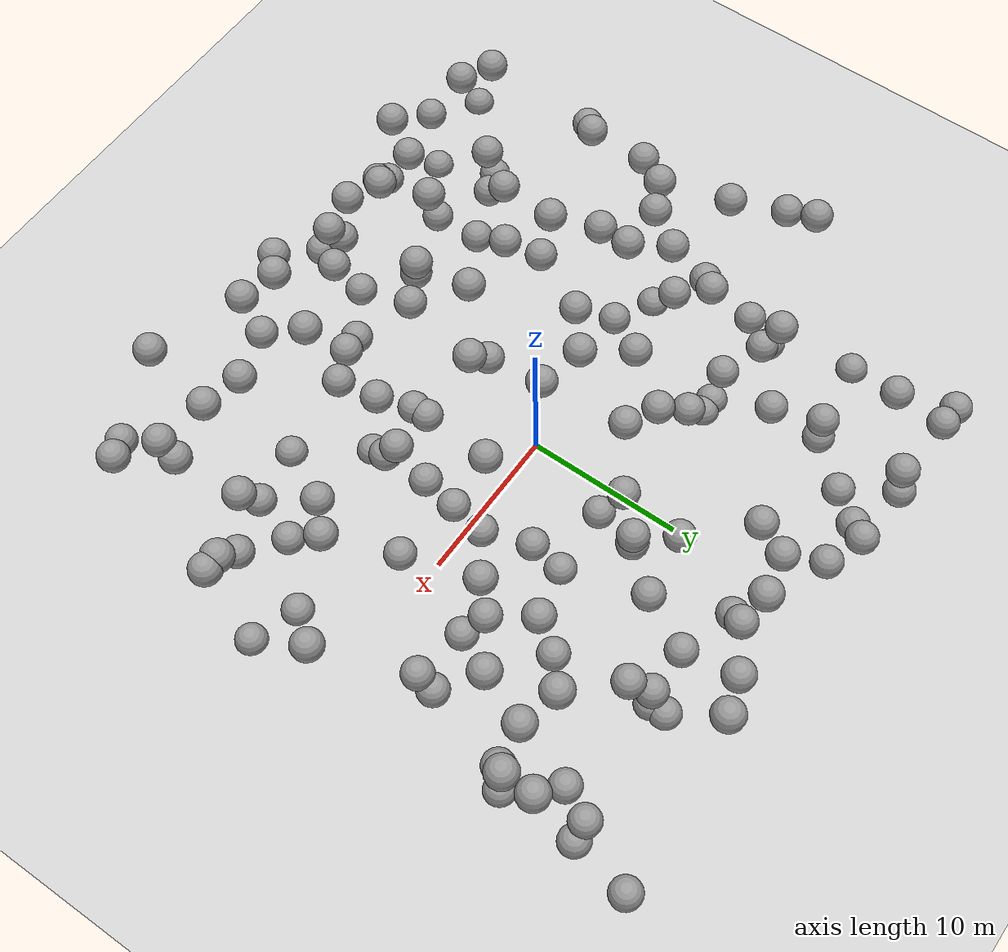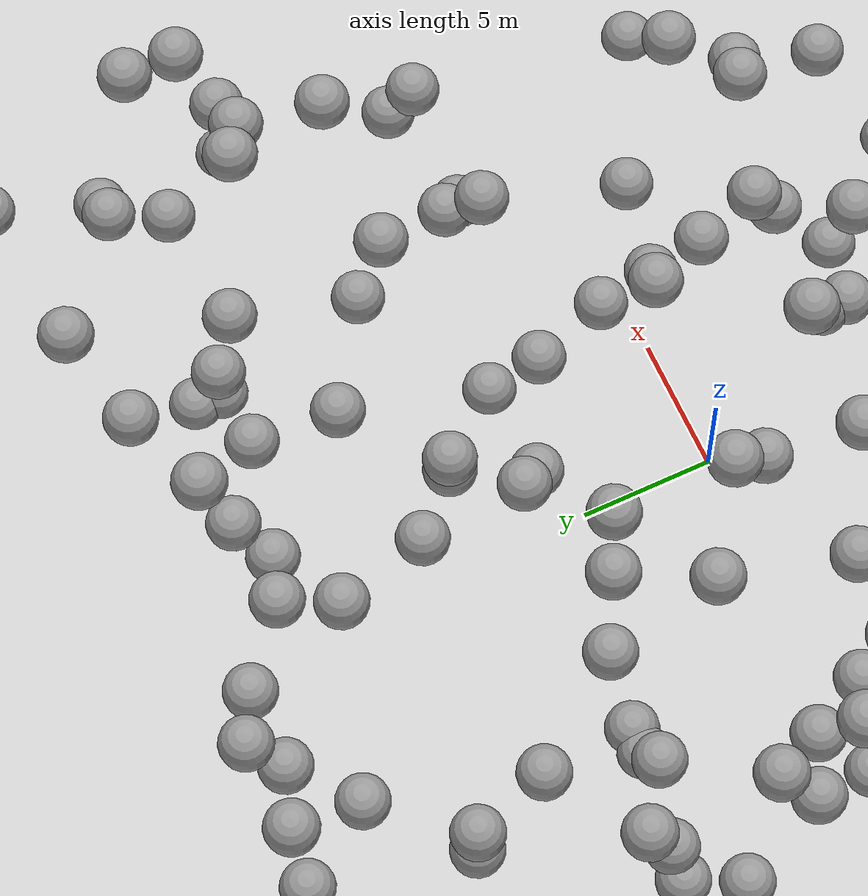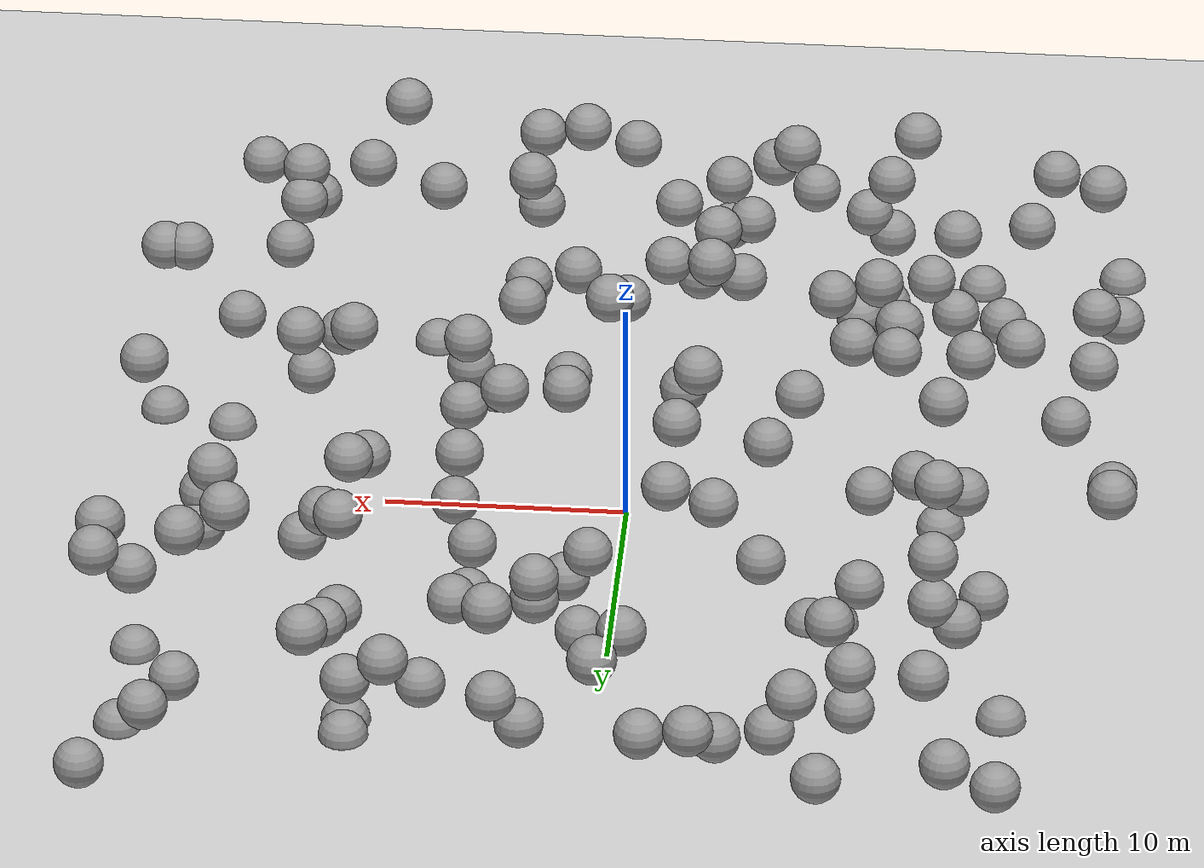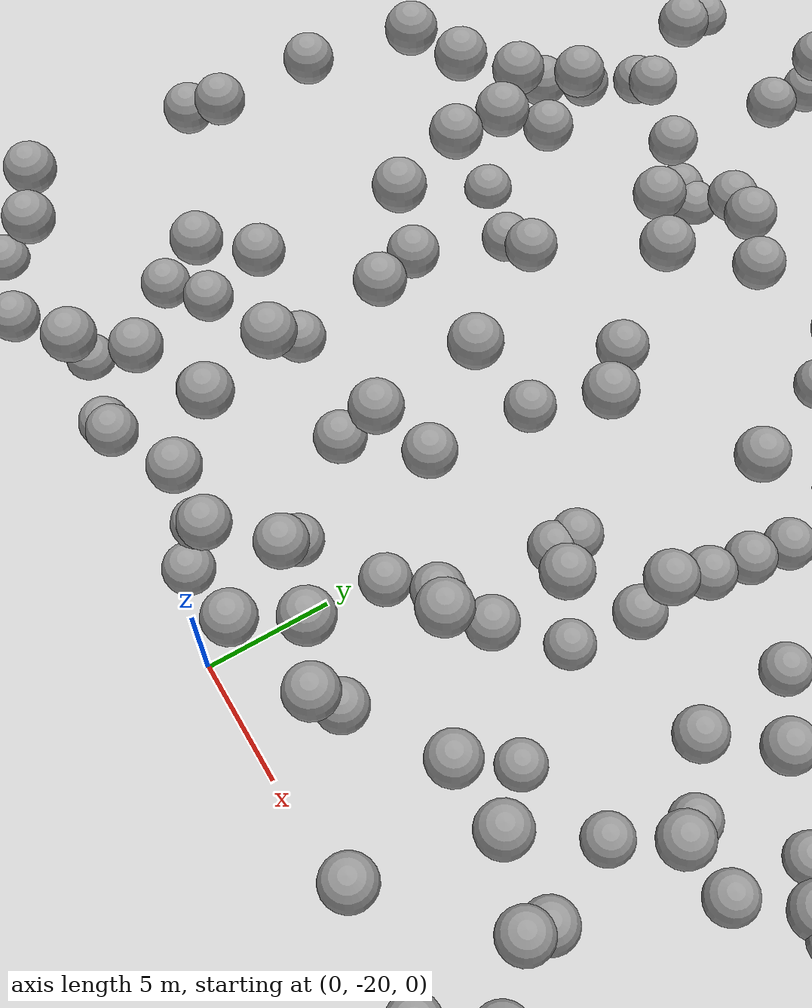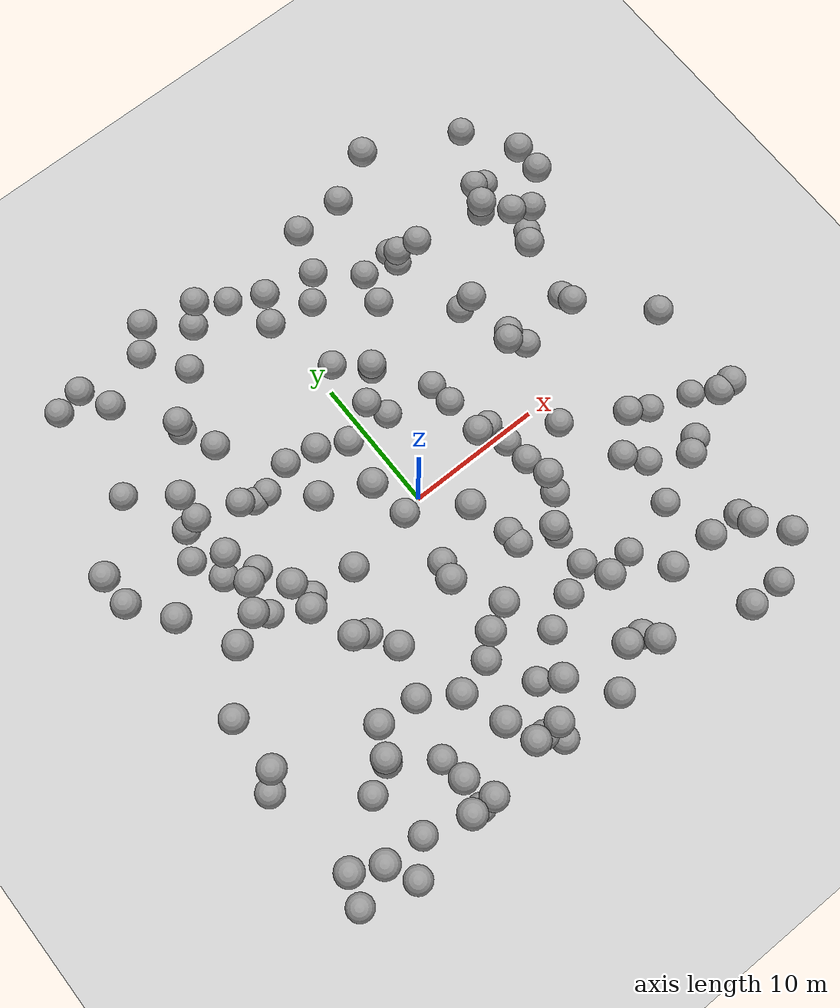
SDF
<?xml version="1.0" ?>
<sdf version='1.7'>
  <world name='default'>
    <light name='sun' type='directional'>
      <cast_shadows>1</cast_shadows>
      <pose>0 0 10 0 -0 0</pose>
      <diffuse>0.8 0.8 0.8 1</diffuse>
      <specular>0.2 0.2 0.2 1</specular>
      <attenuation>
        <range>1000</range>
        <constant>0.9</constant>
        <linear>0.01</linear>
        <quadratic>0.001</quadratic>
      </attenuation>
      <direction>-0.5 0.1 -0.9</direction>
      <spot>
        <inner_angle>0</inner_angle>
        <outer_angle>0</outer_angle>
        <falloff>0</falloff>
      </spot>
    </light>
    <model name='ground_plane'>
      <static>1</static>
      <link name='link'>
        <collision name='collision'>
          <geometry>
            <plane>
              <normal>0 0 1</normal>
              <size>100 100</size>
            </plane>
          </geometry>
          <surface>
            <contact>
              <collide_bitmask>65535</collide_bitmask>
              <ode/>
            </contact>
            <friction>
              <ode>
                <mu>100</mu>
                <mu2>50</mu2>
              </ode>
              <torsional>
                <ode/>
              </torsional>
            </friction>
            <bounce/>
          </surface>
          <max_contacts>10</max_contacts>
        </collision>
        <visual name='visual'>
          <cast_shadows>0</cast_shadows>
          <geometry>
            <plane>
              <normal>0 0 1</normal>
              <size>100 100</size>
            </plane>
          </geometry>
          <material>
            <script>
              <uri>file://media/materials/scripts/gazebo.material</uri>
              <name>Gazebo/Grey</name>
            </script>
          </material>
        </visual>
        <self_collide>0</self_collide>
        <enable_wind>0</enable_wind>
        <kinematic>0</kinematic>
      </link>
    </model>
    <gravity>0 0 -9.8</gravity>
    <magnetic_field>6e-06 2.3e-05 -4.2e-05</magnetic_field>
    <atmosphere type='adiabatic'/>
    <physics type='ode'>
      <max_step_size>0.001</max_step_size>
      <real_time_factor>1</real_time_factor>
      <real_time_update_rate>1000</real_time_update_rate>
    </physics>
    <scene>
      <ambient>0.4 0.4 0.4 1</ambient>
      <background>0.7 0.7 0.7 1</background>
      <shadows>1</shadows>
    </scene>
    <wind/>
    <spherical_coordinates>
      <surface_model>EARTH_WGS84</surface_model>
      <latitude_deg>0</latitude_deg>
      <longitude_deg>0</longitude_deg>
      <elevation>0</elevation>
      <heading_deg>0</heading_deg>
    </spherical_coordinates>

    <model name="sphere_0">
    <static>1</static>
    <pose> 11 9 1 0 0 0 </pose>
      <link name="link">
        <inertial>
          <mass>418.87902047863906</mass>
          <inertia>
            <ixx>167.55160819145564</ixx>
            <iyy>167.55160819145564</iyy>
            <izz>167.55160819145564</izz>
            <ixy>0</ixy>
            <ixz>0</ixz>
            <iyz>0</iyz>
          </inertia>
        </inertial>
        <collision name="collision">
          <geometry>
            <sphere>
              <radius>1.0</radius>
            </sphere>
          </geometry>
        </collision>
        <visual name="visual">
          <geometry>
            <sphere>
              <radius>1.0</radius>
            </sphere>
          </geometry>
          <material>
            <script>
              <uri>file://media/materials/scripts/gazebo.material</uri>
              <name>Gazebo/Grey</name>
            </script>
          </material>
        </visual>
      </link>
    </model>

    <model name="sphere_1">
    <static>1</static>
    <pose> -19 -17 6 0 0 0 </pose>
      <link name="link">
        <inertial>
          <mass>418.87902047863906</mass>
          <inertia>
            <ixx>167.55160819145564</ixx>
            <iyy>167.55160819145564</iyy>
            <izz>167.55160819145564</izz>
            <ixy>0</ixy>
            <ixz>0</ixz>
            <iyz>0</iyz>
          </inertia>
        </inertial>
        <collision name="collision">
          <geometry>
            <sphere>
              <radius>1.0</radius>
            </sphere>
          </geometry>
        </collision>
        <visual name="visual">
          <geometry>
            <sphere>
              <radius>1.0</radius>
            </sphere>
          </geometry>
          <material>
            <script>
              <uri>file://media/materials/scripts/gazebo.material</uri>
              <name>Gazebo/Grey</name>
            </script>
          </material>
        </visual>
      </link>
    </model>

    <model name="sphere_2">
    <static>1</static>
    <pose> -15 -14 1 0 0 0 </pose>
      <link name="link">
        <inertial>
          <mass>418.87902047863906</mass>
          <inertia>
            <ixx>167.55160819145564</ixx>
            <iyy>167.55160819145564</iyy>
            <izz>167.55160819145564</izz>
            <ixy>0</ixy>
            <ixz>0</ixz>
            <iyz>0</iyz>
          </inertia>
        </inertial>
        <collision name="collision">
          <geometry>
            <sphere>
              <radius>1.0</radius>
            </sphere>
          </geometry>
        </collision>
        <visual name="visual">
          <geometry>
            <sphere>
              <radius>1.0</radius>
            </sphere>
          </geometry>
          <material>
            <script>
              <uri>file://media/materials/scripts/gazebo.material</uri>
              <name>Gazebo/Grey</name>
            </script>
          </material>
        </visual>
      </link>
    </model>

    <model name="sphere_3">
    <static>1</static>
    <pose> 1 -4 8 0 0 0 </pose>
      <link name="link">
        <inertial>
          <mass>418.87902047863906</mass>
          <inertia>
            <ixx>167.55160819145564</ixx>
            <iyy>167.55160819145564</iyy>
            <izz>167.55160819145564</izz>
            <ixy>0</ixy>
            <ixz>0</ixz>
            <iyz>0</iyz>
          </inertia>
        </inertial>
        <collision name="collision">
          <geometry>
            <sphere>
              <radius>1.0</radius>
            </sphere>
          </geometry>
        </collision>
        <visual name="visual">
          <geometry>
            <sphere>
              <radius>1.0</radius>
            </sphere>
          </geometry>
          <material>
            <script>
              <uri>file://media/materials/scripts/gazebo.material</uri>
              <name>Gazebo/Grey</name>
            </script>
          </material>
        </visual>
      </link>
    </model>

    <model name="sphere_4">
    <static>1</static>
    <pose> 18 16 1 0 0 0 </pose>
      <link name="link">
        <inertial>
          <mass>418.87902047863906</mass>
          <inertia>
            <ixx>167.55160819145564</ixx>
            <iyy>167.55160819145564</iyy>
            <izz>167.55160819145564</izz>
            <ixy>0</ixy>
            <ixz>0</ixz>
            <iyz>0</iyz>
          </inertia>
        </inertial>
        <collision name="collision">
          <geometry>
            <sphere>
              <radius>1.0</radius>
            </sphere>
          </geometry>
        </collision>
        <visual name="visual">
          <geometry>
            <sphere>
              <radius>1.0</radius>
            </sphere>
          </geometry>
          <material>
            <script>
              <uri>file://media/materials/scripts/gazebo.material</uri>
              <name>Gazebo/Grey</name>
            </script>
          </material>
        </visual>
      </link>
    </model>

    <model name="sphere_5">
    <static>1</static>
    <pose> 11 -2 1 0 0 0 </pose>
      <link name="link">
        <inertial>
          <mass>418.87902047863906</mass>
          <inertia>
            <ixx>167.55160819145564</ixx>
            <iyy>167.55160819145564</iyy>
            <izz>167.55160819145564</izz>
            <ixy>0</ixy>
            <ixz>0</ixz>
            <iyz>0</iyz>
          </inertia>
        </inertial>
        <collision name="collision">
          <geometry>
            <sphere>
              <radius>1.0</radius>
            </sphere>
          </geometry>
        </collision>
        <visual name="visual">
          <geometry>
            <sphere>
              <radius>1.0</radius>
            </sphere>
          </geometry>
          <material>
            <script>
              <uri>file://media/materials/scripts/gazebo.material</uri>
              <name>Gazebo/Grey</name>
            </script>
          </material>
        </visual>
      </link>
    </model>

    <model name="sphere_6">
    <static>1</static>
    <pose> -10 -19 2 0 0 0 </pose>
      <link name="link">
        <inertial>
          <mass>418.87902047863906</mass>
          <inertia>
            <ixx>167.55160819145564</ixx>
            <iyy>167.55160819145564</iyy>
            <izz>167.55160819145564</izz>
            <ixy>0</ixy>
            <ixz>0</ixz>
            <iyz>0</iyz>
          </inertia>
        </inertial>
        <collision name="collision">
          <geometry>
            <sphere>
              <radius>1.0</radius>
            </sphere>
          </geometry>
        </collision>
        <visual name="visual">
          <geometry>
            <sphere>
              <radius>1.0</radius>
            </sphere>
          </geometry>
          <material>
            <script>
              <uri>file://media/materials/scripts/gazebo.material</uri>
              <name>Gazebo/Grey</name>
            </script>
          </material>
        </visual>
      </link>
    </model>

    <model name="sphere_7">
    <static>1</static>
    <pose> 20 -6 0 0 0 0 </pose>
      <link name="link">
        <inertial>
          <mass>418.87902047863906</mass>
          <inertia>
            <ixx>167.55160819145564</ixx>
            <iyy>167.55160819145564</iyy>
            <izz>167.55160819145564</izz>
            <ixy>0</ixy>
            <ixz>0</ixz>
            <iyz>0</iyz>
          </inertia>
        </inertial>
        <collision name="collision">
          <geometry>
            <sphere>
              <radius>1.0</radius>
            </sphere>
          </geometry>
        </collision>
        <visual name="visual">
          <geometry>
            <sphere>
              <radius>1.0</radius>
            </sphere>
          </geometry>
          <material>
            <script>
              <uri>file://media/materials/scripts/gazebo.material</uri>
              <name>Gazebo/Grey</name>
            </script>
          </material>
        </visual>
      </link>
    </model>

    <model name="sphere_8">
    <static>1</static>
    <pose> 5 -17 4 0 0 0 </pose>
      <link name="link">
        <inertial>
          <mass>418.87902047863906</mass>
          <inertia>
            <ixx>167.55160819145564</ixx>
            <iyy>167.55160819145564</iyy>
            <izz>167.55160819145564</izz>
            <ixy>0</ixy>
            <ixz>0</ixz>
            <iyz>0</iyz>
          </inertia>
        </inertial>
        <collision name="collision">
          <geometry>
            <sphere>
              <radius>1.0</radius>
            </sphere>
          </geometry>
        </collision>
        <visual name="visual">
          <geometry>
            <sphere>
              <radius>1.0</radius>
            </sphere>
          </geometry>
          <material>
            <script>
              <uri>file://media/materials/scripts/gazebo.material</uri>
              <name>Gazebo/Grey</name>
            </script>
          </material>
        </visual>
      </link>
    </model>

    <model name="sphere_9">
    <static>1</static>
    <pose> -3 -11 7 0 0 0 </pose>
      <link name="link">
        <inertial>
          <mass>418.87902047863906</mass>
          <inertia>
            <ixx>167.55160819145564</ixx>
            <iyy>167.55160819145564</iyy>
            <izz>167.55160819145564</izz>
            <ixy>0</ixy>
            <ixz>0</ixz>
            <iyz>0</iyz>
          </inertia>
        </inertial>
        <collision name="collision">
          <geometry>
            <sphere>
              <radius>1.0</radius>
            </sphere>
          </geometry>
        </collision>
        <visual name="visual">
          <geometry>
            <sphere>
              <radius>1.0</radius>
            </sphere>
          </geometry>
          <material>
            <script>
              <uri>file://media/materials/scripts/gazebo.material</uri>
              <name>Gazebo/Grey</name>
            </script>
          </material>
        </visual>
      </link>
    </model>

    <model name="sphere_10">
    <static>1</static>
    <pose> -10 14 3 0 0 0 </pose>
      <link name="link">
        <inertial>
          <mass>418.87902047863906</mass>
          <inertia>
            <ixx>167.55160819145564</ixx>
            <iyy>167.55160819145564</iyy>
            <izz>167.55160819145564</izz>
            <ixy>0</ixy>
            <ixz>0</ixz>
            <iyz>0</iyz>
          </inertia>
        </inertial>
        <collision name="collision">
          <geometry>
            <sphere>
              <radius>1.0</radius>
            </sphere>
          </geometry>
        </collision>
        <visual name="visual">
          <geometry>
            <sphere>
              <radius>1.0</radius>
            </sphere>
          </geometry>
          <material>
            <script>
              <uri>file://media/materials/scripts/gazebo.material</uri>
              <name>Gazebo/Grey</name>
            </script>
          </material>
        </visual>
      </link>
    </model>

    <model name="sphere_11">
    <static>1</static>
    <pose> -16 20 2 0 0 0 </pose>
      <link name="link">
        <inertial>
          <mass>418.87902047863906</mass>
          <inertia>
            <ixx>167.55160819145564</ixx>
            <iyy>167.55160819145564</iyy>
            <izz>167.55160819145564</izz>
            <ixy>0</ixy>
            <ixz>0</ixz>
            <iyz>0</iyz>
          </inertia>
        </inertial>
        <collision name="collision">
          <geometry>
            <sphere>
              <radius>1.0</radius>
            </sphere>
          </geometry>
        </collision>
        <visual name="visual">
          <geometry>
            <sphere>
              <radius>1.0</radius>
            </sphere>
          </geometry>
          <material>
            <script>
              <uri>file://media/materials/scripts/gazebo.material</uri>
              <name>Gazebo/Grey</name>
            </script>
          </material>
        </visual>
      </link>
    </model>

    <model name="sphere_12">
    <static>1</static>
    <pose> 0 17 5 0 0 0 </pose>
      <link name="link">
        <inertial>
          <mass>418.87902047863906</mass>
          <inertia>
            <ixx>167.55160819145564</ixx>
            <iyy>167.55160819145564</iyy>
            <izz>167.55160819145564</izz>
            <ixy>0</ixy>
            <ixz>0</ixz>
            <iyz>0</iyz>
          </inertia>
        </inertial>
        <collision name="collision">
          <geometry>
            <sphere>
              <radius>1.0</radius>
            </sphere>
          </geometry>
        </collision>
        <visual name="visual">
          <geometry>
            <sphere>
              <radius>1.0</radius>
            </sphere>
          </geometry>
          <material>
            <script>
              <uri>file://media/materials/scripts/gazebo.material</uri>
              <name>Gazebo/Grey</name>
            </script>
          </material>
        </visual>
      </link>
    </model>

    <model name="sphere_13">
    <static>1</static>
    <pose> 15 12 8 0 0 0 </pose>
      <link name="link">
        <inertial>
          <mass>418.87902047863906</mass>
          <inertia>
            <ixx>167.55160819145564</ixx>
            <iyy>167.55160819145564</iyy>
            <izz>167.55160819145564</izz>
            <ixy>0</ixy>
            <ixz>0</ixz>
            <iyz>0</iyz>
          </inertia>
        </inertial>
        <collision name="collision">
          <geometry>
            <sphere>
              <radius>1.0</radius>
            </sphere>
          </geometry>
        </collision>
        <visual name="visual">
          <geometry>
            <sphere>
              <radius>1.0</radius>
            </sphere>
          </geometry>
          <material>
            <script>
              <uri>file://media/materials/scripts/gazebo.material</uri>
              <name>Gazebo/Grey</name>
            </script>
          </material>
        </visual>
      </link>
    </model>

    <model name="sphere_14">
    <static>1</static>
    <pose> 15 -20 2 0 0 0 </pose>
      <link name="link">
        <inertial>
          <mass>418.87902047863906</mass>
          <inertia>
            <ixx>167.55160819145564</ixx>
            <iyy>167.55160819145564</iyy>
            <izz>167.55160819145564</izz>
            <ixy>0</ixy>
            <ixz>0</ixz>
            <iyz>0</iyz>
          </inertia>
        </inertial>
        <collision name="collision">
          <geometry>
            <sphere>
              <radius>1.0</radius>
            </sphere>
          </geometry>
        </collision>
        <visual name="visual">
          <geometry>
            <sphere>
              <radius>1.0</radius>
            </sphere>
          </geometry>
          <material>
            <script>
              <uri>file://media/materials/scripts/gazebo.material</uri>
              <name>Gazebo/Grey</name>
            </script>
          </material>
        </visual>
      </link>
    </model>

    <model name="sphere_15">
    <static>1</static>
    <pose> 3 -7 2 0 0 0 </pose>
      <link name="link">
        <inertial>
          <mass>418.87902047863906</mass>
          <inertia>
            <ixx>167.55160819145564</ixx>
            <iyy>167.55160819145564</iyy>
            <izz>167.55160819145564</izz>
            <ixy>0</ixy>
            <ixz>0</ixz>
            <iyz>0</iyz>
          </inertia>
        </inertial>
        <collision name="collision">
          <geometry>
            <sphere>
              <radius>1.0</radius>
            </sphere>
          </geometry>
        </collision>
        <visual name="visual">
          <geometry>
            <sphere>
              <radius>1.0</radius>
            </sphere>
          </geometry>
          <material>
            <script>
              <uri>file://media/materials/scripts/gazebo.material</uri>
              <name>Gazebo/Grey</name>
            </script>
          </material>
        </visual>
      </link>
    </model>

    <model name="sphere_16">
    <static>1</static>
    <pose> 5 0 6 0 0 0 </pose>
      <link name="link">
        <inertial>
          <mass>418.87902047863906</mass>
          <inertia>
            <ixx>167.55160819145564</ixx>
            <iyy>167.55160819145564</iyy>
            <izz>167.55160819145564</izz>
            <ixy>0</ixy>
            <ixz>0</ixz>
            <iyz>0</iyz>
          </inertia>
        </inertial>
        <collision name="collision">
          <geometry>
            <sphere>
              <radius>1.0</radius>
            </sphere>
          </geometry>
        </collision>
        <visual name="visual">
          <geometry>
            <sphere>
              <radius>1.0</radius>
            </sphere>
          </geometry>
          <material>
            <script>
              <uri>file://media/materials/scripts/gazebo.material</uri>
              <name>Gazebo/Grey</name>
            </script>
          </material>
        </visual>
      </link>
    </model>

    <model name="sphere_17">
    <static>1</static>
    <pose> 4 18 8 0 0 0 </pose>
      <link name="link">
        <inertial>
          <mass>418.87902047863906</mass>
          <inertia>
            <ixx>167.55160819145564</ixx>
            <iyy>167.55160819145564</iyy>
            <izz>167.55160819145564</izz>
            <ixy>0</ixy>
            <ixz>0</ixz>
            <iyz>0</iyz>
          </inertia>
        </inertial>
        <collision name="collision">
          <geometry>
            <sphere>
              <radius>1.0</radius>
            </sphere>
          </geometry>
        </collision>
        <visual name="visual">
          <geometry>
            <sphere>
              <radius>1.0</radius>
            </sphere>
          </geometry>
          <material>
            <script>
              <uri>file://media/materials/scripts/gazebo.material</uri>
              <name>Gazebo/Grey</name>
            </script>
          </material>
        </visual>
      </link>
    </model>

    <model name="sphere_18">
    <static>1</static>
    <pose> 5 -11 4 0 0 0 </pose>
      <link name="link">
        <inertial>
          <mass>418.87902047863906</mass>
          <inertia>
            <ixx>167.55160819145564</ixx>
            <iyy>167.55160819145564</iyy>
            <izz>167.55160819145564</izz>
            <ixy>0</ixy>
            <ixz>0</ixz>
            <iyz>0</iyz>
          </inertia>
        </inertial>
        <collision name="collision">
          <geometry>
            <sphere>
              <radius>1.0</radius>
            </sphere>
          </geometry>
        </collision>
        <visual name="visual">
          <geometry>
            <sphere>
              <radius>1.0</radius>
            </sphere>
          </geometry>
          <material>
            <script>
              <uri>file://media/materials/scripts/gazebo.material</uri>
              <name>Gazebo/Grey</name>
            </script>
          </material>
        </visual>
      </link>
    </model>

    <model name="sphere_19">
    <static>1</static>
    <pose> 15 -10 6 0 0 0 </pose>
      <link name="link">
        <inertial>
          <mass>418.87902047863906</mass>
          <inertia>
            <ixx>167.55160819145564</ixx>
            <iyy>167.55160819145564</iyy>
            <izz>167.55160819145564</izz>
            <ixy>0</ixy>
            <ixz>0</ixz>
            <iyz>0</iyz>
          </inertia>
        </inertial>
        <collision name="collision">
          <geometry>
            <sphere>
              <radius>1.0</radius>
            </sphere>
          </geometry>
        </collision>
        <visual name="visual">
          <geometry>
            <sphere>
              <radius>1.0</radius>
            </sphere>
          </geometry>
          <material>
            <script>
              <uri>file://media/materials/scripts/gazebo.material</uri>
              <name>Gazebo/Grey</name>
            </script>
          </material>
        </visual>
      </link>
    </model>

    <model name="sphere_20">
    <static>1</static>
    <pose> -3 -18 5 0 0 0 </pose>
      <link name="link">
        <inertial>
          <mass>418.87902047863906</mass>
          <inertia>
            <ixx>167.55160819145564</ixx>
            <iyy>167.55160819145564</iyy>
            <izz>167.55160819145564</izz>
            <ixy>0</ixy>
            <ixz>0</ixz>
            <iyz>0</iyz>
          </inertia>
        </inertial>
        <collision name="collision">
          <geometry>
            <sphere>
              <radius>1.0</radius>
            </sphere>
          </geometry>
        </collision>
        <visual name="visual">
          <geometry>
            <sphere>
              <radius>1.0</radius>
            </sphere>
          </geometry>
          <material>
            <script>
              <uri>file://media/materials/scripts/gazebo.material</uri>
              <name>Gazebo/Grey</name>
            </script>
          </material>
        </visual>
      </link>
    </model>

    <model name="sphere_21">
    <static>1</static>
    <pose> 17 5 2 0 0 0 </pose>
      <link name="link">
        <inertial>
          <mass>418.87902047863906</mass>
          <inertia>
            <ixx>167.55160819145564</ixx>
            <iyy>167.55160819145564</iyy>
            <izz>167.55160819145564</izz>
            <ixy>0</ixy>
            <ixz>0</ixz>
            <iyz>0</iyz>
          </inertia>
        </inertial>
        <collision name="collision">
          <geometry>
            <sphere>
              <radius>1.0</radius>
            </sphere>
          </geometry>
        </collision>
        <visual name="visual">
          <geometry>
            <sphere>
              <radius>1.0</radius>
            </sphere>
          </geometry>
          <material>
            <script>
              <uri>file://media/materials/scripts/gazebo.material</uri>
              <name>Gazebo/Grey</name>
            </script>
          </material>
        </visual>
      </link>
    </model>

    <model name="sphere_22">
    <static>1</static>
    <pose> 5 -8 5 0 0 0 </pose>
      <link name="link">
        <inertial>
          <mass>418.87902047863906</mass>
          <inertia>
            <ixx>167.55160819145564</ixx>
            <iyy>167.55160819145564</iyy>
            <izz>167.55160819145564</izz>
            <ixy>0</ixy>
            <ixz>0</ixz>
            <iyz>0</iyz>
          </inertia>
        </inertial>
        <collision name="collision">
          <geometry>
            <sphere>
              <radius>1.0</radius>
            </sphere>
          </geometry>
        </collision>
        <visual name="visual">
          <geometry>
            <sphere>
              <radius>1.0</radius>
            </sphere>
          </geometry>
          <material>
            <script>
              <uri>file://media/materials/scripts/gazebo.material</uri>
              <name>Gazebo/Grey</name>
            </script>
          </material>
        </visual>
      </link>
    </model>

    <model name="sphere_23">
    <static>1</static>
    <pose> 6 4 1 0 0 0 </pose>
      <link name="link">
        <inertial>
          <mass>418.87902047863906</mass>
          <inertia>
            <ixx>167.55160819145564</ixx>
            <iyy>167.55160819145564</iyy>
            <izz>167.55160819145564</izz>
            <ixy>0</ixy>
            <ixz>0</ixz>
            <iyz>0</iyz>
          </inertia>
        </inertial>
        <collision name="collision">
          <geometry>
            <sphere>
              <radius>1.0</radius>
            </sphere>
          </geometry>
        </collision>
        <visual name="visual">
          <geometry>
            <sphere>
              <radius>1.0</radius>
            </sphere>
          </geometry>
          <material>
            <script>
              <uri>file://media/materials/scripts/gazebo.material</uri>
              <name>Gazebo/Grey</name>
            </script>
          </material>
        </visual>
      </link>
    </model>

    <model name="sphere_24">
    <static>1</static>
    <pose> -9 -6 5 0 0 0 </pose>
      <link name="link">
        <inertial>
          <mass>418.87902047863906</mass>
          <inertia>
            <ixx>167.55160819145564</ixx>
            <iyy>167.55160819145564</iyy>
            <izz>167.55160819145564</izz>
            <ixy>0</ixy>
            <ixz>0</ixz>
            <iyz>0</iyz>
          </inertia>
        </inertial>
        <collision name="collision">
          <geometry>
            <sphere>
              <radius>1.0</radius>
            </sphere>
          </geometry>
        </collision>
        <visual name="visual">
          <geometry>
            <sphere>
              <radius>1.0</radius>
            </sphere>
          </geometry>
          <material>
            <script>
              <uri>file://media/materials/scripts/gazebo.material</uri>
              <name>Gazebo/Grey</name>
            </script>
          </material>
        </visual>
      </link>
    </model>

    <model name="sphere_25">
    <static>1</static>
    <pose> -10 -1 1 0 0 0 </pose>
      <link name="link">
        <inertial>
          <mass>418.87902047863906</mass>
          <inertia>
            <ixx>167.55160819145564</ixx>
            <iyy>167.55160819145564</iyy>
            <izz>167.55160819145564</izz>
            <ixy>0</ixy>
            <ixz>0</ixz>
            <iyz>0</iyz>
          </inertia>
        </inertial>
        <collision name="collision">
          <geometry>
            <sphere>
              <radius>1.0</radius>
            </sphere>
          </geometry>
        </collision>
        <visual name="visual">
          <geometry>
            <sphere>
              <radius>1.0</radius>
            </sphere>
          </geometry>
          <material>
            <script>
              <uri>file://media/materials/scripts/gazebo.material</uri>
              <name>Gazebo/Grey</name>
            </script>
          </material>
        </visual>
      </link>
    </model>

    <model name="sphere_26">
    <static>1</static>
    <pose> 9 -12 0 0 0 0 </pose>
      <link name="link">
        <inertial>
          <mass>418.87902047863906</mass>
          <inertia>
            <ixx>167.55160819145564</ixx>
            <iyy>167.55160819145564</iyy>
            <izz>167.55160819145564</izz>
            <ixy>0</ixy>
            <ixz>0</ixz>
            <iyz>0</iyz>
          </inertia>
        </inertial>
        <collision name="collision">
          <geometry>
            <sphere>
              <radius>1.0</radius>
            </sphere>
          </geometry>
        </collision>
        <visual name="visual">
          <geometry>
            <sphere>
              <radius>1.0</radius>
            </sphere>
          </geometry>
          <material>
            <script>
              <uri>file://media/materials/scripts/gazebo.material</uri>
              <name>Gazebo/Grey</name>
            </script>
          </material>
        </visual>
      </link>
    </model>

    <model name="sphere_27">
    <static>1</static>
    <pose> -19 -9 5 0 0 0 </pose>
      <link name="link">
        <inertial>
          <mass>418.87902047863906</mass>
          <inertia>
            <ixx>167.55160819145564</ixx>
            <iyy>167.55160819145564</iyy>
            <izz>167.55160819145564</izz>
            <ixy>0</ixy>
            <ixz>0</ixz>
            <iyz>0</iyz>
          </inertia>
        </inertial>
        <collision name="collision">
          <geometry>
            <sphere>
              <radius>1.0</radius>
            </sphere>
          </geometry>
        </collision>
        <visual name="visual">
          <geometry>
            <sphere>
              <radius>1.0</radius>
            </sphere>
          </geometry>
          <material>
            <script>
              <uri>file://media/materials/scripts/gazebo.material</uri>
              <name>Gazebo/Grey</name>
            </script>
          </material>
        </visual>
      </link>
    </model>

    <model name="sphere_28">
    <static>1</static>
    <pose> -13 8 2 0 0 0 </pose>
      <link name="link">
        <inertial>
          <mass>418.87902047863906</mass>
          <inertia>
            <ixx>167.55160819145564</ixx>
            <iyy>167.55160819145564</iyy>
            <izz>167.55160819145564</izz>
            <ixy>0</ixy>
            <ixz>0</ixz>
            <iyz>0</iyz>
          </inertia>
        </inertial>
        <collision name="collision">
          <geometry>
            <sphere>
              <radius>1.0</radius>
            </sphere>
          </geometry>
        </collision>
        <visual name="visual">
          <geometry>
            <sphere>
              <radius>1.0</radius>
            </sphere>
          </geometry>
          <material>
            <script>
              <uri>file://media/materials/scripts/gazebo.material</uri>
              <name>Gazebo/Grey</name>
            </script>
          </material>
        </visual>
      </link>
    </model>

    <model name="sphere_29">
    <static>1</static>
    <pose> 15 -15 5 0 0 0 </pose>
      <link name="link">
        <inertial>
          <mass>418.87902047863906</mass>
          <inertia>
            <ixx>167.55160819145564</ixx>
            <iyy>167.55160819145564</iyy>
            <izz>167.55160819145564</izz>
            <ixy>0</ixy>
            <ixz>0</ixz>
            <iyz>0</iyz>
          </inertia>
        </inertial>
        <collision name="collision">
          <geometry>
            <sphere>
              <radius>1.0</radius>
            </sphere>
          </geometry>
        </collision>
        <visual name="visual">
          <geometry>
            <sphere>
              <radius>1.0</radius>
            </sphere>
          </geometry>
          <material>
            <script>
              <uri>file://media/materials/scripts/gazebo.material</uri>
              <name>Gazebo/Grey</name>
            </script>
          </material>
        </visual>
      </link>
    </model>

    <model name="sphere_30">
    <static>1</static>
    <pose> 6 -8 0 0 0 0 </pose>
      <link name="link">
        <inertial>
          <mass>418.87902047863906</mass>
          <inertia>
            <ixx>167.55160819145564</ixx>
            <iyy>167.55160819145564</iyy>
            <izz>167.55160819145564</izz>
            <ixy>0</ixy>
            <ixz>0</ixz>
            <iyz>0</iyz>
          </inertia>
        </inertial>
        <collision name="collision">
          <geometry>
            <sphere>
              <radius>1.0</radius>
            </sphere>
          </geometry>
        </collision>
        <visual name="visual">
          <geometry>
            <sphere>
              <radius>1.0</radius>
            </sphere>
          </geometry>
          <material>
            <script>
              <uri>file://media/materials/scripts/gazebo.material</uri>
              <name>Gazebo/Grey</name>
            </script>
          </material>
        </visual>
      </link>
    </model>

    <model name="sphere_31">
    <static>1</static>
    <pose> 10 16 0 0 0 0 </pose>
      <link name="link">
        <inertial>
          <mass>418.87902047863906</mass>
          <inertia>
            <ixx>167.55160819145564</ixx>
            <iyy>167.55160819145564</iyy>
            <izz>167.55160819145564</izz>
            <ixy>0</ixy>
            <ixz>0</ixz>
            <iyz>0</iyz>
          </inertia>
        </inertial>
        <collision name="collision">
          <geometry>
            <sphere>
              <radius>1.0</radius>
            </sphere>
          </geometry>
        </collision>
        <visual name="visual">
          <geometry>
            <sphere>
              <radius>1.0</radius>
            </sphere>
          </geometry>
          <material>
            <script>
              <uri>file://media/materials/scripts/gazebo.material</uri>
              <name>Gazebo/Grey</name>
            </script>
          </material>
        </visual>
      </link>
    </model>

    <model name="sphere_32">
    <static>1</static>
    <pose> 14 -8 1 0 0 0 </pose>
      <link name="link">
        <inertial>
          <mass>418.87902047863906</mass>
          <inertia>
            <ixx>167.55160819145564</ixx>
            <iyy>167.55160819145564</iyy>
            <izz>167.55160819145564</izz>
            <ixy>0</ixy>
            <ixz>0</ixz>
            <iyz>0</iyz>
          </inertia>
        </inertial>
        <collision name="collision">
          <geometry>
            <sphere>
              <radius>1.0</radius>
            </sphere>
          </geometry>
        </collision>
        <visual name="visual">
          <geometry>
            <sphere>
              <radius>1.0</radius>
            </sphere>
          </geometry>
          <material>
            <script>
              <uri>file://media/materials/scripts/gazebo.material</uri>
              <name>Gazebo/Grey</name>
            </script>
          </material>
        </visual>
      </link>
    </model>

    <model name="sphere_33">
    <static>1</static>
    <pose> 11 -20 7 0 0 0 </pose>
      <link name="link">
        <inertial>
          <mass>418.87902047863906</mass>
          <inertia>
            <ixx>167.55160819145564</ixx>
            <iyy>167.55160819145564</iyy>
            <izz>167.55160819145564</izz>
            <ixy>0</ixy>
            <ixz>0</ixz>
            <iyz>0</iyz>
          </inertia>
        </inertial>
        <collision name="collision">
          <geometry>
            <sphere>
              <radius>1.0</radius>
            </sphere>
          </geometry>
        </collision>
        <visual name="visual">
          <geometry>
            <sphere>
              <radius>1.0</radius>
            </sphere>
          </geometry>
          <material>
            <script>
              <uri>file://media/materials/scripts/gazebo.material</uri>
              <name>Gazebo/Grey</name>
            </script>
          </material>
        </visual>
      </link>
    </model>

    <model name="sphere_34">
    <static>1</static>
    <pose> 17 14 1 0 0 0 </pose>
      <link name="link">
        <inertial>
          <mass>418.87902047863906</mass>
          <inertia>
            <ixx>167.55160819145564</ixx>
            <iyy>167.55160819145564</iyy>
            <izz>167.55160819145564</izz>
            <ixy>0</ixy>
            <ixz>0</ixz>
            <iyz>0</iyz>
          </inertia>
        </inertial>
        <collision name="collision">
          <geometry>
            <sphere>
              <radius>1.0</radius>
            </sphere>
          </geometry>
        </collision>
        <visual name="visual">
          <geometry>
            <sphere>
              <radius>1.0</radius>
            </sphere>
          </geometry>
          <material>
            <script>
              <uri>file://media/materials/scripts/gazebo.material</uri>
              <name>Gazebo/Grey</name>
            </script>
          </material>
        </visual>
      </link>
    </model>

    <model name="sphere_35">
    <static>1</static>
    <pose> -11 -3 8 0 0 0 </pose>
      <link name="link">
        <inertial>
          <mass>418.87902047863906</mass>
          <inertia>
            <ixx>167.55160819145564</ixx>
            <iyy>167.55160819145564</iyy>
            <izz>167.55160819145564</izz>
            <ixy>0</ixy>
            <ixz>0</ixz>
            <iyz>0</iyz>
          </inertia>
        </inertial>
        <collision name="collision">
          <geometry>
            <sphere>
              <radius>1.0</radius>
            </sphere>
          </geometry>
        </collision>
        <visual name="visual">
          <geometry>
            <sphere>
              <radius>1.0</radius>
            </sphere>
          </geometry>
          <material>
            <script>
              <uri>file://media/materials/scripts/gazebo.material</uri>
              <name>Gazebo/Grey</name>
            </script>
          </material>
        </visual>
      </link>
    </model>

    <model name="sphere_36">
    <static>1</static>
    <pose> -20 -10 4 0 0 0 </pose>
      <link name="link">
        <inertial>
          <mass>418.87902047863906</mass>
          <inertia>
            <ixx>167.55160819145564</ixx>
            <iyy>167.55160819145564</iyy>
            <izz>167.55160819145564</izz>
            <ixy>0</ixy>
            <ixz>0</ixz>
            <iyz>0</iyz>
          </inertia>
        </inertial>
        <collision name="collision">
          <geometry>
            <sphere>
              <radius>1.0</radius>
            </sphere>
          </geometry>
        </collision>
        <visual name="visual">
          <geometry>
            <sphere>
              <radius>1.0</radius>
            </sphere>
          </geometry>
          <material>
            <script>
              <uri>file://media/materials/scripts/gazebo.material</uri>
              <name>Gazebo/Grey</name>
            </script>
          </material>
        </visual>
      </link>
    </model>

    <model name="sphere_37">
    <static>1</static>
    <pose> -11 -19 7 0 0 0 </pose>
      <link name="link">
        <inertial>
          <mass>418.87902047863906</mass>
          <inertia>
            <ixx>167.55160819145564</ixx>
            <iyy>167.55160819145564</iyy>
            <izz>167.55160819145564</izz>
            <ixy>0</ixy>
            <ixz>0</ixz>
            <iyz>0</iyz>
          </inertia>
        </inertial>
        <collision name="collision">
          <geometry>
            <sphere>
              <radius>1.0</radius>
            </sphere>
          </geometry>
        </collision>
        <visual name="visual">
          <geometry>
            <sphere>
              <radius>1.0</radius>
            </sphere>
          </geometry>
          <material>
            <script>
              <uri>file://media/materials/scripts/gazebo.material</uri>
              <name>Gazebo/Grey</name>
            </script>
          </material>
        </visual>
      </link>
    </model>

    <model name="sphere_38">
    <static>1</static>
    <pose> 7 1 1 0 0 0 </pose>
      <link name="link">
        <inertial>
          <mass>418.87902047863906</mass>
          <inertia>
            <ixx>167.55160819145564</ixx>
            <iyy>167.55160819145564</iyy>
            <izz>167.55160819145564</izz>
            <ixy>0</ixy>
            <ixz>0</ixz>
            <iyz>0</iyz>
          </inertia>
        </inertial>
        <collision name="collision">
          <geometry>
            <sphere>
              <radius>1.0</radius>
            </sphere>
          </geometry>
        </collision>
        <visual name="visual">
          <geometry>
            <sphere>
              <radius>1.0</radius>
            </sphere>
          </geometry>
          <material>
            <script>
              <uri>file://media/materials/scripts/gazebo.material</uri>
              <name>Gazebo/Grey</name>
            </script>
          </material>
        </visual>
      </link>
    </model>

    <model name="sphere_39">
    <static>1</static>
    <pose> -4 6 5 0 0 0 </pose>
      <link name="link">
        <inertial>
          <mass>418.87902047863906</mass>
          <inertia>
            <ixx>167.55160819145564</ixx>
            <iyy>167.55160819145564</iyy>
            <izz>167.55160819145564</izz>
            <ixy>0</ixy>
            <ixz>0</ixz>
            <iyz>0</iyz>
          </inertia>
        </inertial>
        <collision name="collision">
          <geometry>
            <sphere>
              <radius>1.0</radius>
            </sphere>
          </geometry>
        </collision>
        <visual name="visual">
          <geometry>
            <sphere>
              <radius>1.0</radius>
            </sphere>
          </geometry>
          <material>
            <script>
              <uri>file://media/materials/scripts/gazebo.material</uri>
              <name>Gazebo/Grey</name>
            </script>
          </material>
        </visual>
      </link>
    </model>

    <model name="sphere_40">
    <static>1</static>
    <pose> -20 -19 0 0 0 0 </pose>
      <link name="link">
        <inertial>
          <mass>418.87902047863906</mass>
          <inertia>
            <ixx>167.55160819145564</ixx>
            <iyy>167.55160819145564</iyy>
            <izz>167.55160819145564</izz>
            <ixy>0</ixy>
            <ixz>0</ixz>
            <iyz>0</iyz>
          </inertia>
        </inertial>
        <collision name="collision">
          <geometry>
            <sphere>
              <radius>1.0</radius>
            </sphere>
          </geometry>
        </collision>
        <visual name="visual">
          <geometry>
            <sphere>
              <radius>1.0</radius>
            </sphere>
          </geometry>
          <material>
            <script>
              <uri>file://media/materials/scripts/gazebo.material</uri>
              <name>Gazebo/Grey</name>
            </script>
          </material>
        </visual>
      </link>
    </model>

    <model name="sphere_41">
    <static>1</static>
    <pose> -4 -18 3 0 0 0 </pose>
      <link name="link">
        <inertial>
          <mass>418.87902047863906</mass>
          <inertia>
            <ixx>167.55160819145564</ixx>
            <iyy>167.55160819145564</iyy>
            <izz>167.55160819145564</izz>
            <ixy>0</ixy>
            <ixz>0</ixz>
            <iyz>0</iyz>
          </inertia>
        </inertial>
        <collision name="collision">
          <geometry>
            <sphere>
              <radius>1.0</radius>
            </sphere>
          </geometry>
        </collision>
        <visual name="visual">
          <geometry>
            <sphere>
              <radius>1.0</radius>
            </sphere>
          </geometry>
          <material>
            <script>
              <uri>file://media/materials/scripts/gazebo.material</uri>
              <name>Gazebo/Grey</name>
            </script>
          </material>
        </visual>
      </link>
    </model>

    <model name="sphere_42">
    <static>1</static>
    <pose> 15 -16 6 0 0 0 </pose>
      <link name="link">
        <inertial>
          <mass>418.87902047863906</mass>
          <inertia>
            <ixx>167.55160819145564</ixx>
            <iyy>167.55160819145564</iyy>
            <izz>167.55160819145564</izz>
            <ixy>0</ixy>
            <ixz>0</ixz>
            <iyz>0</iyz>
          </inertia>
        </inertial>
        <collision name="collision">
          <geometry>
            <sphere>
              <radius>1.0</radius>
            </sphere>
          </geometry>
        </collision>
        <visual name="visual">
          <geometry>
            <sphere>
              <radius>1.0</radius>
            </sphere>
          </geometry>
          <material>
            <script>
              <uri>file://media/materials/scripts/gazebo.material</uri>
              <name>Gazebo/Grey</name>
            </script>
          </material>
        </visual>
      </link>
    </model>

    <model name="sphere_43">
    <static>1</static>
    <pose> 4 17 3 0 0 0 </pose>
      <link name="link">
        <inertial>
          <mass>418.87902047863906</mass>
          <inertia>
            <ixx>167.55160819145564</ixx>
            <iyy>167.55160819145564</iyy>
            <izz>167.55160819145564</izz>
            <ixy>0</ixy>
            <ixz>0</ixz>
            <iyz>0</iyz>
          </inertia>
        </inertial>
        <collision name="collision">
          <geometry>
            <sphere>
              <radius>1.0</radius>
            </sphere>
          </geometry>
        </collision>
        <visual name="visual">
          <geometry>
            <sphere>
              <radius>1.0</radius>
            </sphere>
          </geometry>
          <material>
            <script>
              <uri>file://media/materials/scripts/gazebo.material</uri>
              <name>Gazebo/Grey</name>
            </script>
          </material>
        </visual>
      </link>
    </model>

    <model name="sphere_44">
    <static>1</static>
    <pose> -20 5 6 0 0 0 </pose>
      <link name="link">
        <inertial>
          <mass>418.87902047863906</mass>
          <inertia>
            <ixx>167.55160819145564</ixx>
            <iyy>167.55160819145564</iyy>
            <izz>167.55160819145564</izz>
            <ixy>0</ixy>
            <ixz>0</ixz>
            <iyz>0</iyz>
          </inertia>
        </inertial>
        <collision name="collision">
          <geometry>
            <sphere>
              <radius>1.0</radius>
            </sphere>
          </geometry>
        </collision>
        <visual name="visual">
          <geometry>
            <sphere>
              <radius>1.0</radius>
            </sphere>
          </geometry>
          <material>
            <script>
              <uri>file://media/materials/scripts/gazebo.material</uri>
              <name>Gazebo/Grey</name>
            </script>
          </material>
        </visual>
      </link>
    </model>

    <model name="sphere_45">
    <static>1</static>
    <pose> 20 -1 6 0 0 0 </pose>
      <link name="link">
        <inertial>
          <mass>418.87902047863906</mass>
          <inertia>
            <ixx>167.55160819145564</ixx>
            <iyy>167.55160819145564</iyy>
            <izz>167.55160819145564</izz>
            <ixy>0</ixy>
            <ixz>0</ixz>
            <iyz>0</iyz>
          </inertia>
        </inertial>
        <collision name="collision">
          <geometry>
            <sphere>
              <radius>1.0</radius>
            </sphere>
          </geometry>
        </collision>
        <visual name="visual">
          <geometry>
            <sphere>
              <radius>1.0</radius>
            </sphere>
          </geometry>
          <material>
            <script>
              <uri>file://media/materials/scripts/gazebo.material</uri>
              <name>Gazebo/Grey</name>
            </script>
          </material>
        </visual>
      </link>
    </model>

    <model name="sphere_46">
    <static>1</static>
    <pose> -20 7 7 0 0 0 </pose>
      <link name="link">
        <inertial>
          <mass>418.87902047863906</mass>
          <inertia>
            <ixx>167.55160819145564</ixx>
            <iyy>167.55160819145564</iyy>
            <izz>167.55160819145564</izz>
            <ixy>0</ixy>
            <ixz>0</ixz>
            <iyz>0</iyz>
          </inertia>
        </inertial>
        <collision name="collision">
          <geometry>
            <sphere>
              <radius>1.0</radius>
            </sphere>
          </geometry>
        </collision>
        <visual name="visual">
          <geometry>
            <sphere>
              <radius>1.0</radius>
            </sphere>
          </geometry>
          <material>
            <script>
              <uri>file://media/materials/scripts/gazebo.material</uri>
              <name>Gazebo/Grey</name>
            </script>
          </material>
        </visual>
      </link>
    </model>

    <model name="sphere_47">
    <static>1</static>
    <pose> -4 -12 4 0 0 0 </pose>
      <link name="link">
        <inertial>
          <mass>418.87902047863906</mass>
          <inertia>
            <ixx>167.55160819145564</ixx>
            <iyy>167.55160819145564</iyy>
            <izz>167.55160819145564</izz>
            <ixy>0</ixy>
            <ixz>0</ixz>
            <iyz>0</iyz>
          </inertia>
        </inertial>
        <collision name="collision">
          <geometry>
            <sphere>
              <radius>1.0</radius>
            </sphere>
          </geometry>
        </collision>
        <visual name="visual">
          <geometry>
            <sphere>
              <radius>1.0</radius>
            </sphere>
          </geometry>
          <material>
            <script>
              <uri>file://media/materials/scripts/gazebo.material</uri>
              <name>Gazebo/Grey</name>
            </script>
          </material>
        </visual>
      </link>
    </model>

    <model name="sphere_48">
    <static>1</static>
    <pose> -13 -13 6 0 0 0 </pose>
      <link name="link">
        <inertial>
          <mass>418.87902047863906</mass>
          <inertia>
            <ixx>167.55160819145564</ixx>
            <iyy>167.55160819145564</iyy>
            <izz>167.55160819145564</izz>
            <ixy>0</ixy>
            <ixz>0</ixz>
            <iyz>0</iyz>
          </inertia>
        </inertial>
        <collision name="collision">
          <geometry>
            <sphere>
              <radius>1.0</radius>
            </sphere>
          </geometry>
        </collision>
        <visual name="visual">
          <geometry>
            <sphere>
              <radius>1.0</radius>
            </sphere>
          </geometry>
          <material>
            <script>
              <uri>file://media/materials/scripts/gazebo.material</uri>
              <name>Gazebo/Grey</name>
            </script>
          </material>
        </visual>
      </link>
    </model>

    <model name="sphere_49">
    <static>1</static>
    <pose> -11 -1 8 0 0 0 </pose>
      <link name="link">
        <inertial>
          <mass>418.87902047863906</mass>
          <inertia>
            <ixx>167.55160819145564</ixx>
            <iyy>167.55160819145564</iyy>
            <izz>167.55160819145564</izz>
            <ixy>0</ixy>
            <ixz>0</ixz>
            <iyz>0</iyz>
          </inertia>
        </inertial>
        <collision name="collision">
          <geometry>
            <sphere>
              <radius>1.0</radius>
            </sphere>
          </geometry>
        </collision>
        <visual name="visual">
          <geometry>
            <sphere>
              <radius>1.0</radius>
            </sphere>
          </geometry>
          <material>
            <script>
              <uri>file://media/materials/scripts/gazebo.material</uri>
              <name>Gazebo/Grey</name>
            </script>
          </material>
        </visual>
      </link>
    </model>

    <model name="sphere_50">
    <static>1</static>
    <pose> 20 12 7 0 0 0 </pose>
      <link name="link">
        <inertial>
          <mass>418.87902047863906</mass>
          <inertia>
            <ixx>167.55160819145564</ixx>
            <iyy>167.55160819145564</iyy>
            <izz>167.55160819145564</izz>
            <ixy>0</ixy>
            <ixz>0</ixz>
            <iyz>0</iyz>
          </inertia>
        </inertial>
        <collision name="collision">
          <geometry>
            <sphere>
              <radius>1.0</radius>
            </sphere>
          </geometry>
        </collision>
        <visual name="visual">
          <geometry>
            <sphere>
              <radius>1.0</radius>
            </sphere>
          </geometry>
          <material>
            <script>
              <uri>file://media/materials/scripts/gazebo.material</uri>
              <name>Gazebo/Grey</name>
            </script>
          </material>
        </visual>
      </link>
    </model>

    <model name="sphere_51">
    <static>1</static>
    <pose> -9 -11 3 0 0 0 </pose>
      <link name="link">
        <inertial>
          <mass>418.87902047863906</mass>
          <inertia>
            <ixx>167.55160819145564</ixx>
            <iyy>167.55160819145564</iyy>
            <izz>167.55160819145564</izz>
            <ixy>0</ixy>
            <ixz>0</ixz>
            <iyz>0</iyz>
          </inertia>
        </inertial>
        <collision name="collision">
          <geometry>
            <sphere>
              <radius>1.0</radius>
            </sphere>
          </geometry>
        </collision>
        <visual name="visual">
          <geometry>
            <sphere>
              <radius>1.0</radius>
            </sphere>
          </geometry>
          <material>
            <script>
              <uri>file://media/materials/scripts/gazebo.material</uri>
              <name>Gazebo/Grey</name>
            </script>
          </material>
        </visual>
      </link>
    </model>

    <model name="sphere_52">
    <static>1</static>
    <pose> 1 11 2 0 0 0 </pose>
      <link name="link">
        <inertial>
          <mass>418.87902047863906</mass>
          <inertia>
            <ixx>167.55160819145564</ixx>
            <iyy>167.55160819145564</iyy>
            <izz>167.55160819145564</izz>
            <ixy>0</ixy>
            <ixz>0</ixz>
            <iyz>0</iyz>
          </inertia>
        </inertial>
        <collision name="collision">
          <geometry>
            <sphere>
              <radius>1.0</radius>
            </sphere>
          </geometry>
        </collision>
        <visual name="visual">
          <geometry>
            <sphere>
              <radius>1.0</radius>
            </sphere>
          </geometry>
          <material>
            <script>
              <uri>file://media/materials/scripts/gazebo.material</uri>
              <name>Gazebo/Grey</name>
            </script>
          </material>
        </visual>
      </link>
    </model>

    <model name="sphere_53">
    <static>1</static>
    <pose> 9 -15 6 0 0 0 </pose>
      <link name="link">
        <inertial>
          <mass>418.87902047863906</mass>
          <inertia>
            <ixx>167.55160819145564</ixx>
            <iyy>167.55160819145564</iyy>
            <izz>167.55160819145564</izz>
            <ixy>0</ixy>
            <ixz>0</ixz>
            <iyz>0</iyz>
          </inertia>
        </inertial>
        <collision name="collision">
          <geometry>
            <sphere>
              <radius>1.0</radius>
            </sphere>
          </geometry>
        </collision>
        <visual name="visual">
          <geometry>
            <sphere>
              <radius>1.0</radius>
            </sphere>
          </geometry>
          <material>
            <script>
              <uri>file://media/materials/scripts/gazebo.material</uri>
              <name>Gazebo/Grey</name>
            </script>
          </material>
        </visual>
      </link>
    </model>

    <model name="sphere_54">
    <static>1</static>
    <pose> -13 1 7 0 0 0 </pose>
      <link name="link">
        <inertial>
          <mass>418.87902047863906</mass>
          <inertia>
            <ixx>167.55160819145564</ixx>
            <iyy>167.55160819145564</iyy>
            <izz>167.55160819145564</izz>
            <ixy>0</ixy>
            <ixz>0</ixz>
            <iyz>0</iyz>
          </inertia>
        </inertial>
        <collision name="collision">
          <geometry>
            <sphere>
              <radius>1.0</radius>
            </sphere>
          </geometry>
        </collision>
        <visual name="visual">
          <geometry>
            <sphere>
              <radius>1.0</radius>
            </sphere>
          </geometry>
          <material>
            <script>
              <uri>file://media/materials/scripts/gazebo.material</uri>
              <name>Gazebo/Grey</name>
            </script>
          </material>
        </visual>
      </link>
    </model>

    <model name="sphere_55">
    <static>1</static>
    <pose> 11 8 5 0 0 0 </pose>
      <link name="link">
        <inertial>
          <mass>418.87902047863906</mass>
          <inertia>
            <ixx>167.55160819145564</ixx>
            <iyy>167.55160819145564</iyy>
            <izz>167.55160819145564</izz>
            <ixy>0</ixy>
            <ixz>0</ixz>
            <iyz>0</iyz>
          </inertia>
        </inertial>
        <collision name="collision">
          <geometry>
            <sphere>
              <radius>1.0</radius>
            </sphere>
          </geometry>
        </collision>
        <visual name="visual">
          <geometry>
            <sphere>
              <radius>1.0</radius>
            </sphere>
          </geometry>
          <material>
            <script>
              <uri>file://media/materials/scripts/gazebo.material</uri>
              <name>Gazebo/Grey</name>
            </script>
          </material>
        </visual>
      </link>
    </model>

    <model name="sphere_56">
    <static>1</static>
    <pose> -16 13 0 0 0 0 </pose>
      <link name="link">
        <inertial>
          <mass>418.87902047863906</mass>
          <inertia>
            <ixx>167.55160819145564</ixx>
            <iyy>167.55160819145564</iyy>
            <izz>167.55160819145564</izz>
            <ixy>0</ixy>
            <ixz>0</ixz>
            <iyz>0</iyz>
          </inertia>
        </inertial>
        <collision name="collision">
          <geometry>
            <sphere>
              <radius>1.0</radius>
            </sphere>
          </geometry>
        </collision>
        <visual name="visual">
          <geometry>
            <sphere>
              <radius>1.0</radius>
            </sphere>
          </geometry>
          <material>
            <script>
              <uri>file://media/materials/scripts/gazebo.material</uri>
              <name>Gazebo/Grey</name>
            </script>
          </material>
        </visual>
      </link>
    </model>

    <model name="sphere_57">
    <static>1</static>
    <pose> 3 9 3 0 0 0 </pose>
      <link name="link">
        <inertial>
          <mass>418.87902047863906</mass>
          <inertia>
            <ixx>167.55160819145564</ixx>
            <iyy>167.55160819145564</iyy>
            <izz>167.55160819145564</izz>
            <ixy>0</ixy>
            <ixz>0</ixz>
            <iyz>0</iyz>
          </inertia>
        </inertial>
        <collision name="collision">
          <geometry>
            <sphere>
              <radius>1.0</radius>
            </sphere>
          </geometry>
        </collision>
        <visual name="visual">
          <geometry>
            <sphere>
              <radius>1.0</radius>
            </sphere>
          </geometry>
          <material>
            <script>
              <uri>file://media/materials/scripts/gazebo.material</uri>
              <name>Gazebo/Grey</name>
            </script>
          </material>
        </visual>
      </link>
    </model>

    <model name="sphere_58">
    <static>1</static>
    <pose> -4 20 4 0 0 0 </pose>
      <link name="link">
        <inertial>
          <mass>418.87902047863906</mass>
          <inertia>
            <ixx>167.55160819145564</ixx>
            <iyy>167.55160819145564</iyy>
            <izz>167.55160819145564</izz>
            <ixy>0</ixy>
            <ixz>0</ixz>
            <iyz>0</iyz>
          </inertia>
        </inertial>
        <collision name="collision">
          <geometry>
            <sphere>
              <radius>1.0</radius>
            </sphere>
          </geometry>
        </collision>
        <visual name="visual">
          <geometry>
            <sphere>
              <radius>1.0</radius>
            </sphere>
          </geometry>
          <material>
            <script>
              <uri>file://media/materials/scripts/gazebo.material</uri>
              <name>Gazebo/Grey</name>
            </script>
          </material>
        </visual>
      </link>
    </model>

    <model name="sphere_59">
    <static>1</static>
    <pose> -14 -18 0 0 0 0 </pose>
      <link name="link">
        <inertial>
          <mass>418.87902047863906</mass>
          <inertia>
            <ixx>167.55160819145564</ixx>
            <iyy>167.55160819145564</iyy>
            <izz>167.55160819145564</izz>
            <ixy>0</ixy>
            <ixz>0</ixz>
            <iyz>0</iyz>
          </inertia>
        </inertial>
        <collision name="collision">
          <geometry>
            <sphere>
              <radius>1.0</radius>
            </sphere>
          </geometry>
        </collision>
        <visual name="visual">
          <geometry>
            <sphere>
              <radius>1.0</radius>
            </sphere>
          </geometry>
          <material>
            <script>
              <uri>file://media/materials/scripts/gazebo.material</uri>
              <name>Gazebo/Grey</name>
            </script>
          </material>
        </visual>
      </link>
    </model>

    <model name="sphere_60">
    <static>1</static>
    <pose> -3 -7 8 0 0 0 </pose>
      <link name="link">
        <inertial>
          <mass>418.87902047863906</mass>
          <inertia>
            <ixx>167.55160819145564</ixx>
            <iyy>167.55160819145564</iyy>
            <izz>167.55160819145564</izz>
            <ixy>0</ixy>
            <ixz>0</ixz>
            <iyz>0</iyz>
          </inertia>
        </inertial>
        <collision name="collision">
          <geometry>
            <sphere>
              <radius>1.0</radius>
            </sphere>
          </geometry>
        </collision>
        <visual name="visual">
          <geometry>
            <sphere>
              <radius>1.0</radius>
            </sphere>
          </geometry>
          <material>
            <script>
              <uri>file://media/materials/scripts/gazebo.material</uri>
              <name>Gazebo/Grey</name>
            </script>
          </material>
        </visual>
      </link>
    </model>

    <model name="sphere_61">
    <static>1</static>
    <pose> 19 11 0 0 0 0 </pose>
      <link name="link">
        <inertial>
          <mass>418.87902047863906</mass>
          <inertia>
            <ixx>167.55160819145564</ixx>
            <iyy>167.55160819145564</iyy>
            <izz>167.55160819145564</izz>
            <ixy>0</ixy>
            <ixz>0</ixz>
            <iyz>0</iyz>
          </inertia>
        </inertial>
        <collision name="collision">
          <geometry>
            <sphere>
              <radius>1.0</radius>
            </sphere>
          </geometry>
        </collision>
        <visual name="visual">
          <geometry>
            <sphere>
              <radius>1.0</radius>
            </sphere>
          </geometry>
          <material>
            <script>
              <uri>file://media/materials/scripts/gazebo.material</uri>
              <name>Gazebo/Grey</name>
            </script>
          </material>
        </visual>
      </link>
    </model>

    <model name="sphere_62">
    <static>1</static>
    <pose> 3 -12 4 0 0 0 </pose>
      <link name="link">
        <inertial>
          <mass>418.87902047863906</mass>
          <inertia>
            <ixx>167.55160819145564</ixx>
            <iyy>167.55160819145564</iyy>
            <izz>167.55160819145564</izz>
            <ixy>0</ixy>
            <ixz>0</ixz>
            <iyz>0</iyz>
          </inertia>
        </inertial>
        <collision name="collision">
          <geometry>
            <sphere>
              <radius>1.0</radius>
            </sphere>
          </geometry>
        </collision>
        <visual name="visual">
          <geometry>
            <sphere>
              <radius>1.0</radius>
            </sphere>
          </geometry>
          <material>
            <script>
              <uri>file://media/materials/scripts/gazebo.material</uri>
              <name>Gazebo/Grey</name>
            </script>
          </material>
        </visual>
      </link>
    </model>

    <model name="sphere_63">
    <static>1</static>
    <pose> 6 6 0 0 0 0 </pose>
      <link name="link">
        <inertial>
          <mass>418.87902047863906</mass>
          <inertia>
            <ixx>167.55160819145564</ixx>
            <iyy>167.55160819145564</iyy>
            <izz>167.55160819145564</izz>
            <ixy>0</ixy>
            <ixz>0</ixz>
            <iyz>0</iyz>
          </inertia>
        </inertial>
        <collision name="collision">
          <geometry>
            <sphere>
              <radius>1.0</radius>
            </sphere>
          </geometry>
        </collision>
        <visual name="visual">
          <geometry>
            <sphere>
              <radius>1.0</radius>
            </sphere>
          </geometry>
          <material>
            <script>
              <uri>file://media/materials/scripts/gazebo.material</uri>
              <name>Gazebo/Grey</name>
            </script>
          </material>
        </visual>
      </link>
    </model>

    <model name="sphere_64">
    <static>1</static>
    <pose> 13 4 1 0 0 0 </pose>
      <link name="link">
        <inertial>
          <mass>418.87902047863906</mass>
          <inertia>
            <ixx>167.55160819145564</ixx>
            <iyy>167.55160819145564</iyy>
            <izz>167.55160819145564</izz>
            <ixy>0</ixy>
            <ixz>0</ixz>
            <iyz>0</iyz>
          </inertia>
        </inertial>
        <collision name="collision">
          <geometry>
            <sphere>
              <radius>1.0</radius>
            </sphere>
          </geometry>
        </collision>
        <visual name="visual">
          <geometry>
            <sphere>
              <radius>1.0</radius>
            </sphere>
          </geometry>
          <material>
            <script>
              <uri>file://media/materials/scripts/gazebo.material</uri>
              <name>Gazebo/Grey</name>
            </script>
          </material>
        </visual>
      </link>
    </model>

    <model name="sphere_65">
    <static>1</static>
    <pose> -9 -19 3 0 0 0 </pose>
      <link name="link">
        <inertial>
          <mass>418.87902047863906</mass>
          <inertia>
            <ixx>167.55160819145564</ixx>
            <iyy>167.55160819145564</iyy>
            <izz>167.55160819145564</izz>
            <ixy>0</ixy>
            <ixz>0</ixz>
            <iyz>0</iyz>
          </inertia>
        </inertial>
        <collision name="collision">
          <geometry>
            <sphere>
              <radius>1.0</radius>
            </sphere>
          </geometry>
        </collision>
        <visual name="visual">
          <geometry>
            <sphere>
              <radius>1.0</radius>
            </sphere>
          </geometry>
          <material>
            <script>
              <uri>file://media/materials/scripts/gazebo.material</uri>
              <name>Gazebo/Grey</name>
            </script>
          </material>
        </visual>
      </link>
    </model>

    <model name="sphere_66">
    <static>1</static>
    <pose> 13 -11 1 0 0 0 </pose>
      <link name="link">
        <inertial>
          <mass>418.87902047863906</mass>
          <inertia>
            <ixx>167.55160819145564</ixx>
            <iyy>167.55160819145564</iyy>
            <izz>167.55160819145564</izz>
            <ixy>0</ixy>
            <ixz>0</ixz>
            <iyz>0</iyz>
          </inertia>
        </inertial>
        <collision name="collision">
          <geometry>
            <sphere>
              <radius>1.0</radius>
            </sphere>
          </geometry>
        </collision>
        <visual name="visual">
          <geometry>
            <sphere>
              <radius>1.0</radius>
            </sphere>
          </geometry>
          <material>
            <script>
              <uri>file://media/materials/scripts/gazebo.material</uri>
              <name>Gazebo/Grey</name>
            </script>
          </material>
        </visual>
      </link>
    </model>

    <model name="sphere_67">
    <static>1</static>
    <pose> -10 -15 1 0 0 0 </pose>
      <link name="link">
        <inertial>
          <mass>418.87902047863906</mass>
          <inertia>
            <ixx>167.55160819145564</ixx>
            <iyy>167.55160819145564</iyy>
            <izz>167.55160819145564</izz>
            <ixy>0</ixy>
            <ixz>0</ixz>
            <iyz>0</iyz>
          </inertia>
        </inertial>
        <collision name="collision">
          <geometry>
            <sphere>
              <radius>1.0</radius>
            </sphere>
          </geometry>
        </collision>
        <visual name="visual">
          <geometry>
            <sphere>
              <radius>1.0</radius>
            </sphere>
          </geometry>
          <material>
            <script>
              <uri>file://media/materials/scripts/gazebo.material</uri>
              <name>Gazebo/Grey</name>
            </script>
          </material>
        </visual>
      </link>
    </model>

    <model name="sphere_68">
    <static>1</static>
    <pose> 12 -7 4 0 0 0 </pose>
      <link name="link">
        <inertial>
          <mass>418.87902047863906</mass>
          <inertia>
            <ixx>167.55160819145564</ixx>
            <iyy>167.55160819145564</iyy>
            <izz>167.55160819145564</izz>
            <ixy>0</ixy>
            <ixz>0</ixz>
            <iyz>0</iyz>
          </inertia>
        </inertial>
        <collision name="collision">
          <geometry>
            <sphere>
              <radius>1.0</radius>
            </sphere>
          </geometry>
        </collision>
        <visual name="visual">
          <geometry>
            <sphere>
              <radius>1.0</radius>
            </sphere>
          </geometry>
          <material>
            <script>
              <uri>file://media/materials/scripts/gazebo.material</uri>
              <name>Gazebo/Grey</name>
            </script>
          </material>
        </visual>
      </link>
    </model>

    <model name="sphere_69">
    <static>1</static>
    <pose> -14 20 3 0 0 0 </pose>
      <link name="link">
        <inertial>
          <mass>418.87902047863906</mass>
          <inertia>
            <ixx>167.55160819145564</ixx>
            <iyy>167.55160819145564</iyy>
            <izz>167.55160819145564</izz>
            <ixy>0</ixy>
            <ixz>0</ixz>
            <iyz>0</iyz>
          </inertia>
        </inertial>
        <collision name="collision">
          <geometry>
            <sphere>
              <radius>1.0</radius>
            </sphere>
          </geometry>
        </collision>
        <visual name="visual">
          <geometry>
            <sphere>
              <radius>1.0</radius>
            </sphere>
          </geometry>
          <material>
            <script>
              <uri>file://media/materials/scripts/gazebo.material</uri>
              <name>Gazebo/Grey</name>
            </script>
          </material>
        </visual>
      </link>
    </model>

    <model name="sphere_70">
    <static>1</static>
    <pose> -7 17 2 0 0 0 </pose>
      <link name="link">
        <inertial>
          <mass>418.87902047863906</mass>
          <inertia>
            <ixx>167.55160819145564</ixx>
            <iyy>167.55160819145564</iyy>
            <izz>167.55160819145564</izz>
            <ixy>0</ixy>
            <ixz>0</ixz>
            <iyz>0</iyz>
          </inertia>
        </inertial>
        <collision name="collision">
          <geometry>
            <sphere>
              <radius>1.0</radius>
            </sphere>
          </geometry>
        </collision>
        <visual name="visual">
          <geometry>
            <sphere>
              <radius>1.0</radius>
            </sphere>
          </geometry>
          <material>
            <script>
              <uri>file://media/materials/scripts/gazebo.material</uri>
              <name>Gazebo/Grey</name>
            </script>
          </material>
        </visual>
      </link>
    </model>

    <model name="sphere_71">
    <static>1</static>
    <pose> 20 20 1 0 0 0 </pose>
      <link name="link">
        <inertial>
          <mass>418.87902047863906</mass>
          <inertia>
            <ixx>167.55160819145564</ixx>
            <iyy>167.55160819145564</iyy>
            <izz>167.55160819145564</izz>
            <ixy>0</ixy>
            <ixz>0</ixz>
            <iyz>0</iyz>
          </inertia>
        </inertial>
        <collision name="collision">
          <geometry>
            <sphere>
              <radius>1.0</radius>
            </sphere>
          </geometry>
        </collision>
        <visual name="visual">
          <geometry>
            <sphere>
              <radius>1.0</radius>
            </sphere>
          </geometry>
          <material>
            <script>
              <uri>file://media/materials/scripts/gazebo.material</uri>
              <name>Gazebo/Grey</name>
            </script>
          </material>
        </visual>
      </link>
    </model>

    <model name="sphere_72">
    <static>1</static>
    <pose> 12 -15 7 0 0 0 </pose>
      <link name="link">
        <inertial>
          <mass>418.87902047863906</mass>
          <inertia>
            <ixx>167.55160819145564</ixx>
            <iyy>167.55160819145564</iyy>
            <izz>167.55160819145564</izz>
            <ixy>0</ixy>
            <ixz>0</ixz>
            <iyz>0</iyz>
          </inertia>
        </inertial>
        <collision name="collision">
          <geometry>
            <sphere>
              <radius>1.0</radius>
            </sphere>
          </geometry>
        </collision>
        <visual name="visual">
          <geometry>
            <sphere>
              <radius>1.0</radius>
            </sphere>
          </geometry>
          <material>
            <script>
              <uri>file://media/materials/scripts/gazebo.material</uri>
              <name>Gazebo/Grey</name>
            </script>
          </material>
        </visual>
      </link>
    </model>

    <model name="sphere_73">
    <static>1</static>
    <pose> -5 19 3 0 0 0 </pose>
      <link name="link">
        <inertial>
          <mass>418.87902047863906</mass>
          <inertia>
            <ixx>167.55160819145564</ixx>
            <iyy>167.55160819145564</iyy>
            <izz>167.55160819145564</izz>
            <ixy>0</ixy>
            <ixz>0</ixz>
            <iyz>0</iyz>
          </inertia>
        </inertial>
        <collision name="collision">
          <geometry>
            <sphere>
              <radius>1.0</radius>
            </sphere>
          </geometry>
        </collision>
        <visual name="visual">
          <geometry>
            <sphere>
              <radius>1.0</radius>
            </sphere>
          </geometry>
          <material>
            <script>
              <uri>file://media/materials/scripts/gazebo.material</uri>
              <name>Gazebo/Grey</name>
            </script>
          </material>
        </visual>
      </link>
    </model>

    <model name="sphere_74">
    <static>1</static>
    <pose> -6 3 6 0 0 0 </pose>
      <link name="link">
        <inertial>
          <mass>418.87902047863906</mass>
          <inertia>
            <ixx>167.55160819145564</ixx>
            <iyy>167.55160819145564</iyy>
            <izz>167.55160819145564</izz>
            <ixy>0</ixy>
            <ixz>0</ixz>
            <iyz>0</iyz>
          </inertia>
        </inertial>
        <collision name="collision">
          <geometry>
            <sphere>
              <radius>1.0</radius>
            </sphere>
          </geometry>
        </collision>
        <visual name="visual">
          <geometry>
            <sphere>
              <radius>1.0</radius>
            </sphere>
          </geometry>
          <material>
            <script>
              <uri>file://media/materials/scripts/gazebo.material</uri>
              <name>Gazebo/Grey</name>
            </script>
          </material>
        </visual>
      </link>
    </model>

    <model name="sphere_75">
    <static>1</static>
    <pose> -2 -15 2 0 0 0 </pose>
      <link name="link">
        <inertial>
          <mass>418.87902047863906</mass>
          <inertia>
            <ixx>167.55160819145564</ixx>
            <iyy>167.55160819145564</iyy>
            <izz>167.55160819145564</izz>
            <ixy>0</ixy>
            <ixz>0</ixz>
            <iyz>0</iyz>
          </inertia>
        </inertial>
        <collision name="collision">
          <geometry>
            <sphere>
              <radius>1.0</radius>
            </sphere>
          </geometry>
        </collision>
        <visual name="visual">
          <geometry>
            <sphere>
              <radius>1.0</radius>
            </sphere>
          </geometry>
          <material>
            <script>
              <uri>file://media/materials/scripts/gazebo.material</uri>
              <name>Gazebo/Grey</name>
            </script>
          </material>
        </visual>
      </link>
    </model>

    <model name="sphere_76">
    <static>1</static>
    <pose> 1 7 3 0 0 0 </pose>
      <link name="link">
        <inertial>
          <mass>418.87902047863906</mass>
          <inertia>
            <ixx>167.55160819145564</ixx>
            <iyy>167.55160819145564</iyy>
            <izz>167.55160819145564</izz>
            <ixy>0</ixy>
            <ixz>0</ixz>
            <iyz>0</iyz>
          </inertia>
        </inertial>
        <collision name="collision">
          <geometry>
            <sphere>
              <radius>1.0</radius>
            </sphere>
          </geometry>
        </collision>
        <visual name="visual">
          <geometry>
            <sphere>
              <radius>1.0</radius>
            </sphere>
          </geometry>
          <material>
            <script>
              <uri>file://media/materials/scripts/gazebo.material</uri>
              <name>Gazebo/Grey</name>
            </script>
          </material>
        </visual>
      </link>
    </model>

    <model name="sphere_77">
    <static>1</static>
    <pose> 7 -5 5 0 0 0 </pose>
      <link name="link">
        <inertial>
          <mass>418.87902047863906</mass>
          <inertia>
            <ixx>167.55160819145564</ixx>
            <iyy>167.55160819145564</iyy>
            <izz>167.55160819145564</izz>
            <ixy>0</ixy>
            <ixz>0</ixz>
            <iyz>0</iyz>
          </inertia>
        </inertial>
        <collision name="collision">
          <geometry>
            <sphere>
              <radius>1.0</radius>
            </sphere>
          </geometry>
        </collision>
        <visual name="visual">
          <geometry>
            <sphere>
              <radius>1.0</radius>
            </sphere>
          </geometry>
          <material>
            <script>
              <uri>file://media/materials/scripts/gazebo.material</uri>
              <name>Gazebo/Grey</name>
            </script>
          </material>
        </visual>
      </link>
    </model>

    <model name="sphere_78">
    <static>1</static>
    <pose> 1 -19 6 0 0 0 </pose>
      <link name="link">
        <inertial>
          <mass>418.87902047863906</mass>
          <inertia>
            <ixx>167.55160819145564</ixx>
            <iyy>167.55160819145564</iyy>
            <izz>167.55160819145564</izz>
            <ixy>0</ixy>
            <ixz>0</ixz>
            <iyz>0</iyz>
          </inertia>
        </inertial>
        <collision name="collision">
          <geometry>
            <sphere>
              <radius>1.0</radius>
            </sphere>
          </geometry>
        </collision>
        <visual name="visual">
          <geometry>
            <sphere>
              <radius>1.0</radius>
            </sphere>
          </geometry>
          <material>
            <script>
              <uri>file://media/materials/scripts/gazebo.material</uri>
              <name>Gazebo/Grey</name>
            </script>
          </material>
        </visual>
      </link>
    </model>

    <model name="sphere_79">
    <static>1</static>
    <pose> 5 -13 8 0 0 0 </pose>
      <link name="link">
        <inertial>
          <mass>418.87902047863906</mass>
          <inertia>
            <ixx>167.55160819145564</ixx>
            <iyy>167.55160819145564</iyy>
            <izz>167.55160819145564</izz>
            <ixy>0</ixy>
            <ixz>0</ixz>
            <iyz>0</iyz>
          </inertia>
        </inertial>
        <collision name="collision">
          <geometry>
            <sphere>
              <radius>1.0</radius>
            </sphere>
          </geometry>
        </collision>
        <visual name="visual">
          <geometry>
            <sphere>
              <radius>1.0</radius>
            </sphere>
          </geometry>
          <material>
            <script>
              <uri>file://media/materials/scripts/gazebo.material</uri>
              <name>Gazebo/Grey</name>
            </script>
          </material>
        </visual>
      </link>
    </model>

    <model name="sphere_80">
    <static>1</static>
    <pose> -2 19 3 0 0 0 </pose>
      <link name="link">
        <inertial>
          <mass>418.87902047863906</mass>
          <inertia>
            <ixx>167.55160819145564</ixx>
            <iyy>167.55160819145564</iyy>
            <izz>167.55160819145564</izz>
            <ixy>0</ixy>
            <ixz>0</ixz>
            <iyz>0</iyz>
          </inertia>
        </inertial>
        <collision name="collision">
          <geometry>
            <sphere>
              <radius>1.0</radius>
            </sphere>
          </geometry>
        </collision>
        <visual name="visual">
          <geometry>
            <sphere>
              <radius>1.0</radius>
            </sphere>
          </geometry>
          <material>
            <script>
              <uri>file://media/materials/scripts/gazebo.material</uri>
              <name>Gazebo/Grey</name>
            </script>
          </material>
        </visual>
      </link>
    </model>

    <model name="sphere_81">
    <static>1</static>
    <pose> 20 14 7 0 0 0 </pose>
      <link name="link">
        <inertial>
          <mass>418.87902047863906</mass>
          <inertia>
            <ixx>167.55160819145564</ixx>
            <iyy>167.55160819145564</iyy>
            <izz>167.55160819145564</izz>
            <ixy>0</ixy>
            <ixz>0</ixz>
            <iyz>0</iyz>
          </inertia>
        </inertial>
        <collision name="collision">
          <geometry>
            <sphere>
              <radius>1.0</radius>
            </sphere>
          </geometry>
        </collision>
        <visual name="visual">
          <geometry>
            <sphere>
              <radius>1.0</radius>
            </sphere>
          </geometry>
          <material>
            <script>
              <uri>file://media/materials/scripts/gazebo.material</uri>
              <name>Gazebo/Grey</name>
            </script>
          </material>
        </visual>
      </link>
    </model>

    <model name="sphere_82">
    <static>1</static>
    <pose> -13 4 5 0 0 0 </pose>
      <link name="link">
        <inertial>
          <mass>418.87902047863906</mass>
          <inertia>
            <ixx>167.55160819145564</ixx>
            <iyy>167.55160819145564</iyy>
            <izz>167.55160819145564</izz>
            <ixy>0</ixy>
            <ixz>0</ixz>
            <iyz>0</iyz>
          </inertia>
        </inertial>
        <collision name="collision">
          <geometry>
            <sphere>
              <radius>1.0</radius>
            </sphere>
          </geometry>
        </collision>
        <visual name="visual">
          <geometry>
            <sphere>
              <radius>1.0</radius>
            </sphere>
          </geometry>
          <material>
            <script>
              <uri>file://media/materials/scripts/gazebo.material</uri>
              <name>Gazebo/Grey</name>
            </script>
          </material>
        </visual>
      </link>
    </model>

    <model name="sphere_83">
    <static>1</static>
    <pose> -14 8 1 0 0 0 </pose>
      <link name="link">
        <inertial>
          <mass>418.87902047863906</mass>
          <inertia>
            <ixx>167.55160819145564</ixx>
            <iyy>167.55160819145564</iyy>
            <izz>167.55160819145564</izz>
            <ixy>0</ixy>
            <ixz>0</ixz>
            <iyz>0</iyz>
          </inertia>
        </inertial>
        <collision name="collision">
          <geometry>
            <sphere>
              <radius>1.0</radius>
            </sphere>
          </geometry>
        </collision>
        <visual name="visual">
          <geometry>
            <sphere>
              <radius>1.0</radius>
            </sphere>
          </geometry>
          <material>
            <script>
              <uri>file://media/materials/scripts/gazebo.material</uri>
              <name>Gazebo/Grey</name>
            </script>
          </material>
        </visual>
      </link>
    </model>

    <model name="sphere_84">
    <static>1</static>
    <pose> -10 14 1 0 0 0 </pose>
      <link name="link">
        <inertial>
          <mass>418.87902047863906</mass>
          <inertia>
            <ixx>167.55160819145564</ixx>
            <iyy>167.55160819145564</iyy>
            <izz>167.55160819145564</izz>
            <ixy>0</ixy>
            <ixz>0</ixz>
            <iyz>0</iyz>
          </inertia>
        </inertial>
        <collision name="collision">
          <geometry>
            <sphere>
              <radius>1.0</radius>
            </sphere>
          </geometry>
        </collision>
        <visual name="visual">
          <geometry>
            <sphere>
              <radius>1.0</radius>
            </sphere>
          </geometry>
          <material>
            <script>
              <uri>file://media/materials/scripts/gazebo.material</uri>
              <name>Gazebo/Grey</name>
            </script>
          </material>
        </visual>
      </link>
    </model>

    <model name="sphere_85">
    <static>1</static>
    <pose> -10 -17 6 0 0 0 </pose>
      <link name="link">
        <inertial>
          <mass>418.87902047863906</mass>
          <inertia>
            <ixx>167.55160819145564</ixx>
            <iyy>167.55160819145564</iyy>
            <izz>167.55160819145564</izz>
            <ixy>0</ixy>
            <ixz>0</ixz>
            <iyz>0</iyz>
          </inertia>
        </inertial>
        <collision name="collision">
          <geometry>
            <sphere>
              <radius>1.0</radius>
            </sphere>
          </geometry>
        </collision>
        <visual name="visual">
          <geometry>
            <sphere>
              <radius>1.0</radius>
            </sphere>
          </geometry>
          <material>
            <script>
              <uri>file://media/materials/scripts/gazebo.material</uri>
              <name>Gazebo/Grey</name>
            </script>
          </material>
        </visual>
      </link>
    </model>

    <model name="sphere_86">
    <static>1</static>
    <pose> 2 6 1 0 0 0 </pose>
      <link name="link">
        <inertial>
          <mass>418.87902047863906</mass>
          <inertia>
            <ixx>167.55160819145564</ixx>
            <iyy>167.55160819145564</iyy>
            <izz>167.55160819145564</izz>
            <ixy>0</ixy>
            <ixz>0</ixz>
            <iyz>0</iyz>
          </inertia>
        </inertial>
        <collision name="collision">
          <geometry>
            <sphere>
              <radius>1.0</radius>
            </sphere>
          </geometry>
        </collision>
        <visual name="visual">
          <geometry>
            <sphere>
              <radius>1.0</radius>
            </sphere>
          </geometry>
          <material>
            <script>
              <uri>file://media/materials/scripts/gazebo.material</uri>
              <name>Gazebo/Grey</name>
            </script>
          </material>
        </visual>
      </link>
    </model>

    <model name="sphere_87">
    <static>1</static>
    <pose> -12 -11 5 0 0 0 </pose>
      <link name="link">
        <inertial>
          <mass>418.87902047863906</mass>
          <inertia>
            <ixx>167.55160819145564</ixx>
            <iyy>167.55160819145564</iyy>
            <izz>167.55160819145564</izz>
            <ixy>0</ixy>
            <ixz>0</ixz>
            <iyz>0</iyz>
          </inertia>
        </inertial>
        <collision name="collision">
          <geometry>
            <sphere>
              <radius>1.0</radius>
            </sphere>
          </geometry>
        </collision>
        <visual name="visual">
          <geometry>
            <sphere>
              <radius>1.0</radius>
            </sphere>
          </geometry>
          <material>
            <script>
              <uri>file://media/materials/scripts/gazebo.material</uri>
              <name>Gazebo/Grey</name>
            </script>
          </material>
        </visual>
      </link>
    </model>

    <model name="sphere_88">
    <static>1</static>
    <pose> -9 20 2 0 0 0 </pose>
      <link name="link">
        <inertial>
          <mass>418.87902047863906</mass>
          <inertia>
            <ixx>167.55160819145564</ixx>
            <iyy>167.55160819145564</iyy>
            <izz>167.55160819145564</izz>
            <ixy>0</ixy>
            <ixz>0</ixz>
            <iyz>0</iyz>
          </inertia>
        </inertial>
        <collision name="collision">
          <geometry>
            <sphere>
              <radius>1.0</radius>
            </sphere>
          </geometry>
        </collision>
        <visual name="visual">
          <geometry>
            <sphere>
              <radius>1.0</radius>
            </sphere>
          </geometry>
          <material>
            <script>
              <uri>file://media/materials/scripts/gazebo.material</uri>
              <name>Gazebo/Grey</name>
            </script>
          </material>
        </visual>
      </link>
    </model>

    <model name="sphere_89">
    <static>1</static>
    <pose> -12 2 4 0 0 0 </pose>
      <link name="link">
        <inertial>
          <mass>418.87902047863906</mass>
          <inertia>
            <ixx>167.55160819145564</ixx>
            <iyy>167.55160819145564</iyy>
            <izz>167.55160819145564</izz>
            <ixy>0</ixy>
            <ixz>0</ixz>
            <iyz>0</iyz>
          </inertia>
        </inertial>
        <collision name="collision">
          <geometry>
            <sphere>
              <radius>1.0</radius>
            </sphere>
          </geometry>
        </collision>
        <visual name="visual">
          <geometry>
            <sphere>
              <radius>1.0</radius>
            </sphere>
          </geometry>
          <material>
            <script>
              <uri>file://media/materials/scripts/gazebo.material</uri>
              <name>Gazebo/Grey</name>
            </script>
          </material>
        </visual>
      </link>
    </model>

    <model name="sphere_90">
    <static>1</static>
    <pose> -9 11 3 0 0 0 </pose>
      <link name="link">
        <inertial>
          <mass>418.87902047863906</mass>
          <inertia>
            <ixx>167.55160819145564</ixx>
            <iyy>167.55160819145564</iyy>
            <izz>167.55160819145564</izz>
            <ixy>0</ixy>
            <ixz>0</ixz>
            <iyz>0</iyz>
          </inertia>
        </inertial>
        <collision name="collision">
          <geometry>
            <sphere>
              <radius>1.0</radius>
            </sphere>
          </geometry>
        </collision>
        <visual name="visual">
          <geometry>
            <sphere>
              <radius>1.0</radius>
            </sphere>
          </geometry>
          <material>
            <script>
              <uri>file://media/materials/scripts/gazebo.material</uri>
              <name>Gazebo/Grey</name>
            </script>
          </material>
        </visual>
      </link>
    </model>

    <model name="sphere_91">
    <static>1</static>
    <pose> 14 -5 5 0 0 0 </pose>
      <link name="link">
        <inertial>
          <mass>418.87902047863906</mass>
          <inertia>
            <ixx>167.55160819145564</ixx>
            <iyy>167.55160819145564</iyy>
            <izz>167.55160819145564</izz>
            <ixy>0</ixy>
            <ixz>0</ixz>
            <iyz>0</iyz>
          </inertia>
        </inertial>
        <collision name="collision">
          <geometry>
            <sphere>
              <radius>1.0</radius>
            </sphere>
          </geometry>
        </collision>
        <visual name="visual">
          <geometry>
            <sphere>
              <radius>1.0</radius>
            </sphere>
          </geometry>
          <material>
            <script>
              <uri>file://media/materials/scripts/gazebo.material</uri>
              <name>Gazebo/Grey</name>
            </script>
          </material>
        </visual>
      </link>
    </model>

    <model name="sphere_92">
    <static>1</static>
    <pose> -13 9 5 0 0 0 </pose>
      <link name="link">
        <inertial>
          <mass>418.87902047863906</mass>
          <inertia>
            <ixx>167.55160819145564</ixx>
            <iyy>167.55160819145564</iyy>
            <izz>167.55160819145564</izz>
            <ixy>0</ixy>
            <ixz>0</ixz>
            <iyz>0</iyz>
          </inertia>
        </inertial>
        <collision name="collision">
          <geometry>
            <sphere>
              <radius>1.0</radius>
            </sphere>
          </geometry>
        </collision>
        <visual name="visual">
          <geometry>
            <sphere>
              <radius>1.0</radius>
            </sphere>
          </geometry>
          <material>
            <script>
              <uri>file://media/materials/scripts/gazebo.material</uri>
              <name>Gazebo/Grey</name>
            </script>
          </material>
        </visual>
      </link>
    </model>

    <model name="sphere_93">
    <static>1</static>
    <pose> 17 -9 3 0 0 0 </pose>
      <link name="link">
        <inertial>
          <mass>418.87902047863906</mass>
          <inertia>
            <ixx>167.55160819145564</ixx>
            <iyy>167.55160819145564</iyy>
            <izz>167.55160819145564</izz>
            <ixy>0</ixy>
            <ixz>0</ixz>
            <iyz>0</iyz>
          </inertia>
        </inertial>
        <collision name="collision">
          <geometry>
            <sphere>
              <radius>1.0</radius>
            </sphere>
          </geometry>
        </collision>
        <visual name="visual">
          <geometry>
            <sphere>
              <radius>1.0</radius>
            </sphere>
          </geometry>
          <material>
            <script>
              <uri>file://media/materials/scripts/gazebo.material</uri>
              <name>Gazebo/Grey</name>
            </script>
          </material>
        </visual>
      </link>
    </model>

    <model name="sphere_94">
    <static>1</static>
    <pose> 17 -5 0 0 0 0 </pose>
      <link name="link">
        <inertial>
          <mass>418.87902047863906</mass>
          <inertia>
            <ixx>167.55160819145564</ixx>
            <iyy>167.55160819145564</iyy>
            <izz>167.55160819145564</izz>
            <ixy>0</ixy>
            <ixz>0</ixz>
            <iyz>0</iyz>
          </inertia>
        </inertial>
        <collision name="collision">
          <geometry>
            <sphere>
              <radius>1.0</radius>
            </sphere>
          </geometry>
        </collision>
        <visual name="visual">
          <geometry>
            <sphere>
              <radius>1.0</radius>
            </sphere>
          </geometry>
          <material>
            <script>
              <uri>file://media/materials/scripts/gazebo.material</uri>
              <name>Gazebo/Grey</name>
            </script>
          </material>
        </visual>
      </link>
    </model>

    <model name="sphere_95">
    <static>1</static>
    <pose> -1 -10 6 0 0 0 </pose>
      <link name="link">
        <inertial>
          <mass>418.87902047863906</mass>
          <inertia>
            <ixx>167.55160819145564</ixx>
            <iyy>167.55160819145564</iyy>
            <izz>167.55160819145564</izz>
            <ixy>0</ixy>
            <ixz>0</ixz>
            <iyz>0</iyz>
          </inertia>
        </inertial>
        <collision name="collision">
          <geometry>
            <sphere>
              <radius>1.0</radius>
            </sphere>
          </geometry>
        </collision>
        <visual name="visual">
          <geometry>
            <sphere>
              <radius>1.0</radius>
            </sphere>
          </geometry>
          <material>
            <script>
              <uri>file://media/materials/scripts/gazebo.material</uri>
              <name>Gazebo/Grey</name>
            </script>
          </material>
        </visual>
      </link>
    </model>

    <model name="sphere_96">
    <static>1</static>
    <pose> 12 5 3 0 0 0 </pose>
      <link name="link">
        <inertial>
          <mass>418.87902047863906</mass>
          <inertia>
            <ixx>167.55160819145564</ixx>
            <iyy>167.55160819145564</iyy>
            <izz>167.55160819145564</izz>
            <ixy>0</ixy>
            <ixz>0</ixz>
            <iyz>0</iyz>
          </inertia>
        </inertial>
        <collision name="collision">
          <geometry>
            <sphere>
              <radius>1.0</radius>
            </sphere>
          </geometry>
        </collision>
        <visual name="visual">
          <geometry>
            <sphere>
              <radius>1.0</radius>
            </sphere>
          </geometry>
          <material>
            <script>
              <uri>file://media/materials/scripts/gazebo.material</uri>
              <name>Gazebo/Grey</name>
            </script>
          </material>
        </visual>
      </link>
    </model>

    <model name="sphere_97">
    <static>1</static>
    <pose> -2 5 5 0 0 0 </pose>
      <link name="link">
        <inertial>
          <mass>418.87902047863906</mass>
          <inertia>
            <ixx>167.55160819145564</ixx>
            <iyy>167.55160819145564</iyy>
            <izz>167.55160819145564</izz>
            <ixy>0</ixy>
            <ixz>0</ixz>
            <iyz>0</iyz>
          </inertia>
        </inertial>
        <collision name="collision">
          <geometry>
            <sphere>
              <radius>1.0</radius>
            </sphere>
          </geometry>
        </collision>
        <visual name="visual">
          <geometry>
            <sphere>
              <radius>1.0</radius>
            </sphere>
          </geometry>
          <material>
            <script>
              <uri>file://media/materials/scripts/gazebo.material</uri>
              <name>Gazebo/Grey</name>
            </script>
          </material>
        </visual>
      </link>
    </model>

    <model name="sphere_98">
    <static>1</static>
    <pose> -15 6 1 0 0 0 </pose>
      <link name="link">
        <inertial>
          <mass>418.87902047863906</mass>
          <inertia>
            <ixx>167.55160819145564</ixx>
            <iyy>167.55160819145564</iyy>
            <izz>167.55160819145564</izz>
            <ixy>0</ixy>
            <ixz>0</ixz>
            <iyz>0</iyz>
          </inertia>
        </inertial>
        <collision name="collision">
          <geometry>
            <sphere>
              <radius>1.0</radius>
            </sphere>
          </geometry>
        </collision>
        <visual name="visual">
          <geometry>
            <sphere>
              <radius>1.0</radius>
            </sphere>
          </geometry>
          <material>
            <script>
              <uri>file://media/materials/scripts/gazebo.material</uri>
              <name>Gazebo/Grey</name>
            </script>
          </material>
        </visual>
      </link>
    </model>

    <model name="sphere_99">
    <static>1</static>
    <pose> -3 -19 2 0 0 0 </pose>
      <link name="link">
        <inertial>
          <mass>418.87902047863906</mass>
          <inertia>
            <ixx>167.55160819145564</ixx>
            <iyy>167.55160819145564</iyy>
            <izz>167.55160819145564</izz>
            <ixy>0</ixy>
            <ixz>0</ixz>
            <iyz>0</iyz>
          </inertia>
        </inertial>
        <collision name="collision">
          <geometry>
            <sphere>
              <radius>1.0</radius>
            </sphere>
          </geometry>
        </collision>
        <visual name="visual">
          <geometry>
            <sphere>
              <radius>1.0</radius>
            </sphere>
          </geometry>
          <material>
            <script>
              <uri>file://media/materials/scripts/gazebo.material</uri>
              <name>Gazebo/Grey</name>
            </script>
          </material>
        </visual>
      </link>
    </model>

    <model name="sphere_100">
    <static>1</static>
    <pose> 7 -3 3 0 0 0 </pose>
      <link name="link">
        <inertial>
          <mass>418.87902047863906</mass>
          <inertia>
            <ixx>167.55160819145564</ixx>
            <iyy>167.55160819145564</iyy>
            <izz>167.55160819145564</izz>
            <ixy>0</ixy>
            <ixz>0</ixz>
            <iyz>0</iyz>
          </inertia>
        </inertial>
        <collision name="collision">
          <geometry>
            <sphere>
              <radius>1.0</radius>
            </sphere>
          </geometry>
        </collision>
        <visual name="visual">
          <geometry>
            <sphere>
              <radius>1.0</radius>
            </sphere>
          </geometry>
          <material>
            <script>
              <uri>file://media/materials/scripts/gazebo.material</uri>
              <name>Gazebo/Grey</name>
            </script>
          </material>
        </visual>
      </link>
    </model>

    <model name="sphere_101">
    <static>1</static>
    <pose> -14 -1 8 0 0 0 </pose>
      <link name="link">
        <inertial>
          <mass>418.87902047863906</mass>
          <inertia>
            <ixx>167.55160819145564</ixx>
            <iyy>167.55160819145564</iyy>
            <izz>167.55160819145564</izz>
            <ixy>0</ixy>
            <ixz>0</ixz>
            <iyz>0</iyz>
          </inertia>
        </inertial>
        <collision name="collision">
          <geometry>
            <sphere>
              <radius>1.0</radius>
            </sphere>
          </geometry>
        </collision>
        <visual name="visual">
          <geometry>
            <sphere>
              <radius>1.0</radius>
            </sphere>
          </geometry>
          <material>
            <script>
              <uri>file://media/materials/scripts/gazebo.material</uri>
              <name>Gazebo/Grey</name>
            </script>
          </material>
        </visual>
      </link>
    </model>

    <model name="sphere_102">
    <static>1</static>
    <pose> 3 9 2 0 0 0 </pose>
      <link name="link">
        <inertial>
          <mass>418.87902047863906</mass>
          <inertia>
            <ixx>167.55160819145564</ixx>
            <iyy>167.55160819145564</iyy>
            <izz>167.55160819145564</izz>
            <ixy>0</ixy>
            <ixz>0</ixz>
            <iyz>0</iyz>
          </inertia>
        </inertial>
        <collision name="collision">
          <geometry>
            <sphere>
              <radius>1.0</radius>
            </sphere>
          </geometry>
        </collision>
        <visual name="visual">
          <geometry>
            <sphere>
              <radius>1.0</radius>
            </sphere>
          </geometry>
          <material>
            <script>
              <uri>file://media/materials/scripts/gazebo.material</uri>
              <name>Gazebo/Grey</name>
            </script>
          </material>
        </visual>
      </link>
    </model>

    <model name="sphere_103">
    <static>1</static>
    <pose> 7 15 2 0 0 0 </pose>
      <link name="link">
        <inertial>
          <mass>418.87902047863906</mass>
          <inertia>
            <ixx>167.55160819145564</ixx>
            <iyy>167.55160819145564</iyy>
            <izz>167.55160819145564</izz>
            <ixy>0</ixy>
            <ixz>0</ixz>
            <iyz>0</iyz>
          </inertia>
        </inertial>
        <collision name="collision">
          <geometry>
            <sphere>
              <radius>1.0</radius>
            </sphere>
          </geometry>
        </collision>
        <visual name="visual">
          <geometry>
            <sphere>
              <radius>1.0</radius>
            </sphere>
          </geometry>
          <material>
            <script>
              <uri>file://media/materials/scripts/gazebo.material</uri>
              <name>Gazebo/Grey</name>
            </script>
          </material>
        </visual>
      </link>
    </model>

    <model name="sphere_104">
    <static>1</static>
    <pose> -8 20 6 0 0 0 </pose>
      <link name="link">
        <inertial>
          <mass>418.87902047863906</mass>
          <inertia>
            <ixx>167.55160819145564</ixx>
            <iyy>167.55160819145564</iyy>
            <izz>167.55160819145564</izz>
            <ixy>0</ixy>
            <ixz>0</ixz>
            <iyz>0</iyz>
          </inertia>
        </inertial>
        <collision name="collision">
          <geometry>
            <sphere>
              <radius>1.0</radius>
            </sphere>
          </geometry>
        </collision>
        <visual name="visual">
          <geometry>
            <sphere>
              <radius>1.0</radius>
            </sphere>
          </geometry>
          <material>
            <script>
              <uri>file://media/materials/scripts/gazebo.material</uri>
              <name>Gazebo/Grey</name>
            </script>
          </material>
        </visual>
      </link>
    </model>

    <model name="sphere_105">
    <static>1</static>
    <pose> -7 -13 8 0 0 0 </pose>
      <link name="link">
        <inertial>
          <mass>418.87902047863906</mass>
          <inertia>
            <ixx>167.55160819145564</ixx>
            <iyy>167.55160819145564</iyy>
            <izz>167.55160819145564</izz>
            <ixy>0</ixy>
            <ixz>0</ixz>
            <iyz>0</iyz>
          </inertia>
        </inertial>
        <collision name="collision">
          <geometry>
            <sphere>
              <radius>1.0</radius>
            </sphere>
          </geometry>
        </collision>
        <visual name="visual">
          <geometry>
            <sphere>
              <radius>1.0</radius>
            </sphere>
          </geometry>
          <material>
            <script>
              <uri>file://media/materials/scripts/gazebo.material</uri>
              <name>Gazebo/Grey</name>
            </script>
          </material>
        </visual>
      </link>
    </model>

    <model name="sphere_106">
    <static>1</static>
    <pose> -19 -5 5 0 0 0 </pose>
      <link name="link">
        <inertial>
          <mass>418.87902047863906</mass>
          <inertia>
            <ixx>167.55160819145564</ixx>
            <iyy>167.55160819145564</iyy>
            <izz>167.55160819145564</izz>
            <ixy>0</ixy>
            <ixz>0</ixz>
            <iyz>0</iyz>
          </inertia>
        </inertial>
        <collision name="collision">
          <geometry>
            <sphere>
              <radius>1.0</radius>
            </sphere>
          </geometry>
        </collision>
        <visual name="visual">
          <geometry>
            <sphere>
              <radius>1.0</radius>
            </sphere>
          </geometry>
          <material>
            <script>
              <uri>file://media/materials/scripts/gazebo.material</uri>
              <name>Gazebo/Grey</name>
            </script>
          </material>
        </visual>
      </link>
    </model>

    <model name="sphere_107">
    <static>1</static>
    <pose> 10 15 0 0 0 0 </pose>
      <link name="link">
        <inertial>
          <mass>418.87902047863906</mass>
          <inertia>
            <ixx>167.55160819145564</ixx>
            <iyy>167.55160819145564</iyy>
            <izz>167.55160819145564</izz>
            <ixy>0</ixy>
            <ixz>0</ixz>
            <iyz>0</iyz>
          </inertia>
        </inertial>
        <collision name="collision">
          <geometry>
            <sphere>
              <radius>1.0</radius>
            </sphere>
          </geometry>
        </collision>
        <visual name="visual">
          <geometry>
            <sphere>
              <radius>1.0</radius>
            </sphere>
          </geometry>
          <material>
            <script>
              <uri>file://media/materials/scripts/gazebo.material</uri>
              <name>Gazebo/Grey</name>
            </script>
          </material>
        </visual>
      </link>
    </model>

    <model name="sphere_108">
    <static>1</static>
    <pose> -18 2 7 0 0 0 </pose>
      <link name="link">
        <inertial>
          <mass>418.87902047863906</mass>
          <inertia>
            <ixx>167.55160819145564</ixx>
            <iyy>167.55160819145564</iyy>
            <izz>167.55160819145564</izz>
            <ixy>0</ixy>
            <ixz>0</ixz>
            <iyz>0</iyz>
          </inertia>
        </inertial>
        <collision name="collision">
          <geometry>
            <sphere>
              <radius>1.0</radius>
            </sphere>
          </geometry>
        </collision>
        <visual name="visual">
          <geometry>
            <sphere>
              <radius>1.0</radius>
            </sphere>
          </geometry>
          <material>
            <script>
              <uri>file://media/materials/scripts/gazebo.material</uri>
              <name>Gazebo/Grey</name>
            </script>
          </material>
        </visual>
      </link>
    </model>

    <model name="sphere_109">
    <static>1</static>
    <pose> 17 11 6 0 0 0 </pose>
      <link name="link">
        <inertial>
          <mass>418.87902047863906</mass>
          <inertia>
            <ixx>167.55160819145564</ixx>
            <iyy>167.55160819145564</iyy>
            <izz>167.55160819145564</izz>
            <ixy>0</ixy>
            <ixz>0</ixz>
            <iyz>0</iyz>
          </inertia>
        </inertial>
        <collision name="collision">
          <geometry>
            <sphere>
              <radius>1.0</radius>
            </sphere>
          </geometry>
        </collision>
        <visual name="visual">
          <geometry>
            <sphere>
              <radius>1.0</radius>
            </sphere>
          </geometry>
          <material>
            <script>
              <uri>file://media/materials/scripts/gazebo.material</uri>
              <name>Gazebo/Grey</name>
            </script>
          </material>
        </visual>
      </link>
    </model>

    <model name="sphere_110">
    <static>1</static>
    <pose> 7 -6 3 0 0 0 </pose>
      <link name="link">
        <inertial>
          <mass>418.87902047863906</mass>
          <inertia>
            <ixx>167.55160819145564</ixx>
            <iyy>167.55160819145564</iyy>
            <izz>167.55160819145564</izz>
            <ixy>0</ixy>
            <ixz>0</ixz>
            <iyz>0</iyz>
          </inertia>
        </inertial>
        <collision name="collision">
          <geometry>
            <sphere>
              <radius>1.0</radius>
            </sphere>
          </geometry>
        </collision>
        <visual name="visual">
          <geometry>
            <sphere>
              <radius>1.0</radius>
            </sphere>
          </geometry>
          <material>
            <script>
              <uri>file://media/materials/scripts/gazebo.material</uri>
              <name>Gazebo/Grey</name>
            </script>
          </material>
        </visual>
      </link>
    </model>

    <model name="sphere_111">
    <static>1</static>
    <pose> 10 15 2 0 0 0 </pose>
      <link name="link">
        <inertial>
          <mass>418.87902047863906</mass>
          <inertia>
            <ixx>167.55160819145564</ixx>
            <iyy>167.55160819145564</iyy>
            <izz>167.55160819145564</izz>
            <ixy>0</ixy>
            <ixz>0</ixz>
            <iyz>0</iyz>
          </inertia>
        </inertial>
        <collision name="collision">
          <geometry>
            <sphere>
              <radius>1.0</radius>
            </sphere>
          </geometry>
        </collision>
        <visual name="visual">
          <geometry>
            <sphere>
              <radius>1.0</radius>
            </sphere>
          </geometry>
          <material>
            <script>
              <uri>file://media/materials/scripts/gazebo.material</uri>
              <name>Gazebo/Grey</name>
            </script>
          </material>
        </visual>
      </link>
    </model>

    <model name="sphere_112">
    <static>1</static>
    <pose> 11 4 5 0 0 0 </pose>
      <link name="link">
        <inertial>
          <mass>418.87902047863906</mass>
          <inertia>
            <ixx>167.55160819145564</ixx>
            <iyy>167.55160819145564</iyy>
            <izz>167.55160819145564</izz>
            <ixy>0</ixy>
            <ixz>0</ixz>
            <iyz>0</iyz>
          </inertia>
        </inertial>
        <collision name="collision">
          <geometry>
            <sphere>
              <radius>1.0</radius>
            </sphere>
          </geometry>
        </collision>
        <visual name="visual">
          <geometry>
            <sphere>
              <radius>1.0</radius>
            </sphere>
          </geometry>
          <material>
            <script>
              <uri>file://media/materials/scripts/gazebo.material</uri>
              <name>Gazebo/Grey</name>
            </script>
          </material>
        </visual>
      </link>
    </model>

    <model name="sphere_113">
    <static>1</static>
    <pose> -7 -2 5 0 0 0 </pose>
      <link name="link">
        <inertial>
          <mass>418.87902047863906</mass>
          <inertia>
            <ixx>167.55160819145564</ixx>
            <iyy>167.55160819145564</iyy>
            <izz>167.55160819145564</izz>
            <ixy>0</ixy>
            <ixz>0</ixz>
            <iyz>0</iyz>
          </inertia>
        </inertial>
        <collision name="collision">
          <geometry>
            <sphere>
              <radius>1.0</radius>
            </sphere>
          </geometry>
        </collision>
        <visual name="visual">
          <geometry>
            <sphere>
              <radius>1.0</radius>
            </sphere>
          </geometry>
          <material>
            <script>
              <uri>file://media/materials/scripts/gazebo.material</uri>
              <name>Gazebo/Grey</name>
            </script>
          </material>
        </visual>
      </link>
    </model>

    <model name="sphere_114">
    <static>1</static>
    <pose> 17 4 3 0 0 0 </pose>
      <link name="link">
        <inertial>
          <mass>418.87902047863906</mass>
          <inertia>
            <ixx>167.55160819145564</ixx>
            <iyy>167.55160819145564</iyy>
            <izz>167.55160819145564</izz>
            <ixy>0</ixy>
            <ixz>0</ixz>
            <iyz>0</iyz>
          </inertia>
        </inertial>
        <collision name="collision">
          <geometry>
            <sphere>
              <radius>1.0</radius>
            </sphere>
          </geometry>
        </collision>
        <visual name="visual">
          <geometry>
            <sphere>
              <radius>1.0</radius>
            </sphere>
          </geometry>
          <material>
            <script>
              <uri>file://media/materials/scripts/gazebo.material</uri>
              <name>Gazebo/Grey</name>
            </script>
          </material>
        </visual>
      </link>
    </model>

    <model name="sphere_115">
    <static>1</static>
    <pose> -16 -2 8 0 0 0 </pose>
      <link name="link">
        <inertial>
          <mass>418.87902047863906</mass>
          <inertia>
            <ixx>167.55160819145564</ixx>
            <iyy>167.55160819145564</iyy>
            <izz>167.55160819145564</izz>
            <ixy>0</ixy>
            <ixz>0</ixz>
            <iyz>0</iyz>
          </inertia>
        </inertial>
        <collision name="collision">
          <geometry>
            <sphere>
              <radius>1.0</radius>
            </sphere>
          </geometry>
        </collision>
        <visual name="visual">
          <geometry>
            <sphere>
              <radius>1.0</radius>
            </sphere>
          </geometry>
          <material>
            <script>
              <uri>file://media/materials/scripts/gazebo.material</uri>
              <name>Gazebo/Grey</name>
            </script>
          </material>
        </visual>
      </link>
    </model>

    <model name="sphere_116">
    <static>1</static>
    <pose> -6 7 3 0 0 0 </pose>
      <link name="link">
        <inertial>
          <mass>418.87902047863906</mass>
          <inertia>
            <ixx>167.55160819145564</ixx>
            <iyy>167.55160819145564</iyy>
            <izz>167.55160819145564</izz>
            <ixy>0</ixy>
            <ixz>0</ixz>
            <iyz>0</iyz>
          </inertia>
        </inertial>
        <collision name="collision">
          <geometry>
            <sphere>
              <radius>1.0</radius>
            </sphere>
          </geometry>
        </collision>
        <visual name="visual">
          <geometry>
            <sphere>
              <radius>1.0</radius>
            </sphere>
          </geometry>
          <material>
            <script>
              <uri>file://media/materials/scripts/gazebo.material</uri>
              <name>Gazebo/Grey</name>
            </script>
          </material>
        </visual>
      </link>
    </model>

    <model name="sphere_117">
    <static>1</static>
    <pose> 20 -8 7 0 0 0 </pose>
      <link name="link">
        <inertial>
          <mass>418.87902047863906</mass>
          <inertia>
            <ixx>167.55160819145564</ixx>
            <iyy>167.55160819145564</iyy>
            <izz>167.55160819145564</izz>
            <ixy>0</ixy>
            <ixz>0</ixz>
            <iyz>0</iyz>
          </inertia>
        </inertial>
        <collision name="collision">
          <geometry>
            <sphere>
              <radius>1.0</radius>
            </sphere>
          </geometry>
        </collision>
        <visual name="visual">
          <geometry>
            <sphere>
              <radius>1.0</radius>
            </sphere>
          </geometry>
          <material>
            <script>
              <uri>file://media/materials/scripts/gazebo.material</uri>
              <name>Gazebo/Grey</name>
            </script>
          </material>
        </visual>
      </link>
    </model>

    <model name="sphere_118">
    <static>1</static>
    <pose> -16 -20 2 0 0 0 </pose>
      <link name="link">
        <inertial>
          <mass>418.87902047863906</mass>
          <inertia>
            <ixx>167.55160819145564</ixx>
            <iyy>167.55160819145564</iyy>
            <izz>167.55160819145564</izz>
            <ixy>0</ixy>
            <ixz>0</ixz>
            <iyz>0</iyz>
          </inertia>
        </inertial>
        <collision name="collision">
          <geometry>
            <sphere>
              <radius>1.0</radius>
            </sphere>
          </geometry>
        </collision>
        <visual name="visual">
          <geometry>
            <sphere>
              <radius>1.0</radius>
            </sphere>
          </geometry>
          <material>
            <script>
              <uri>file://media/materials/scripts/gazebo.material</uri>
              <name>Gazebo/Grey</name>
            </script>
          </material>
        </visual>
      </link>
    </model>

    <model name="sphere_119">
    <static>1</static>
    <pose> -3 1 8 0 0 0 </pose>
      <link name="link">
        <inertial>
          <mass>418.87902047863906</mass>
          <inertia>
            <ixx>167.55160819145564</ixx>
            <iyy>167.55160819145564</iyy>
            <izz>167.55160819145564</izz>
            <ixy>0</ixy>
            <ixz>0</ixz>
            <iyz>0</iyz>
          </inertia>
        </inertial>
        <collision name="collision">
          <geometry>
            <sphere>
              <radius>1.0</radius>
            </sphere>
          </geometry>
        </collision>
        <visual name="visual">
          <geometry>
            <sphere>
              <radius>1.0</radius>
            </sphere>
          </geometry>
          <material>
            <script>
              <uri>file://media/materials/scripts/gazebo.material</uri>
              <name>Gazebo/Grey</name>
            </script>
          </material>
        </visual>
      </link>
    </model>

    <model name="sphere_120">
    <static>1</static>
    <pose> 11 14 4 0 0 0 </pose>
      <link name="link">
        <inertial>
          <mass>418.87902047863906</mass>
          <inertia>
            <ixx>167.55160819145564</ixx>
            <iyy>167.55160819145564</iyy>
            <izz>167.55160819145564</izz>
            <ixy>0</ixy>
            <ixz>0</ixz>
            <iyz>0</iyz>
          </inertia>
        </inertial>
        <collision name="collision">
          <geometry>
            <sphere>
              <radius>1.0</radius>
            </sphere>
          </geometry>
        </collision>
        <visual name="visual">
          <geometry>
            <sphere>
              <radius>1.0</radius>
            </sphere>
          </geometry>
          <material>
            <script>
              <uri>file://media/materials/scripts/gazebo.material</uri>
              <name>Gazebo/Grey</name>
            </script>
          </material>
        </visual>
      </link>
    </model>

    <model name="sphere_121">
    <static>1</static>
    <pose> -8 -8 6 0 0 0 </pose>
      <link name="link">
        <inertial>
          <mass>418.87902047863906</mass>
          <inertia>
            <ixx>167.55160819145564</ixx>
            <iyy>167.55160819145564</iyy>
            <izz>167.55160819145564</izz>
            <ixy>0</ixy>
            <ixz>0</ixz>
            <iyz>0</iyz>
          </inertia>
        </inertial>
        <collision name="collision">
          <geometry>
            <sphere>
              <radius>1.0</radius>
            </sphere>
          </geometry>
        </collision>
        <visual name="visual">
          <geometry>
            <sphere>
              <radius>1.0</radius>
            </sphere>
          </geometry>
          <material>
            <script>
              <uri>file://media/materials/scripts/gazebo.material</uri>
              <name>Gazebo/Grey</name>
            </script>
          </material>
        </visual>
      </link>
    </model>

    <model name="sphere_122">
    <static>1</static>
    <pose> -13 17 5 0 0 0 </pose>
      <link name="link">
        <inertial>
          <mass>418.87902047863906</mass>
          <inertia>
            <ixx>167.55160819145564</ixx>
            <iyy>167.55160819145564</iyy>
            <izz>167.55160819145564</izz>
            <ixy>0</ixy>
            <ixz>0</ixz>
            <iyz>0</iyz>
          </inertia>
        </inertial>
        <collision name="collision">
          <geometry>
            <sphere>
              <radius>1.0</radius>
            </sphere>
          </geometry>
        </collision>
        <visual name="visual">
          <geometry>
            <sphere>
              <radius>1.0</radius>
            </sphere>
          </geometry>
          <material>
            <script>
              <uri>file://media/materials/scripts/gazebo.material</uri>
              <name>Gazebo/Grey</name>
            </script>
          </material>
        </visual>
      </link>
    </model>

    <model name="sphere_123">
    <static>1</static>
    <pose> 7 -1 2 0 0 0 </pose>
      <link name="link">
        <inertial>
          <mass>418.87902047863906</mass>
          <inertia>
            <ixx>167.55160819145564</ixx>
            <iyy>167.55160819145564</iyy>
            <izz>167.55160819145564</izz>
            <ixy>0</ixy>
            <ixz>0</ixz>
            <iyz>0</iyz>
          </inertia>
        </inertial>
        <collision name="collision">
          <geometry>
            <sphere>
              <radius>1.0</radius>
            </sphere>
          </geometry>
        </collision>
        <visual name="visual">
          <geometry>
            <sphere>
              <radius>1.0</radius>
            </sphere>
          </geometry>
          <material>
            <script>
              <uri>file://media/materials/scripts/gazebo.material</uri>
              <name>Gazebo/Grey</name>
            </script>
          </material>
        </visual>
      </link>
    </model>

    <model name="sphere_124">
    <static>1</static>
    <pose> -10 7 2 0 0 0 </pose>
      <link name="link">
        <inertial>
          <mass>418.87902047863906</mass>
          <inertia>
            <ixx>167.55160819145564</ixx>
            <iyy>167.55160819145564</iyy>
            <izz>167.55160819145564</izz>
            <ixy>0</ixy>
            <ixz>0</ixz>
            <iyz>0</iyz>
          </inertia>
        </inertial>
        <collision name="collision">
          <geometry>
            <sphere>
              <radius>1.0</radius>
            </sphere>
          </geometry>
        </collision>
        <visual name="visual">
          <geometry>
            <sphere>
              <radius>1.0</radius>
            </sphere>
          </geometry>
          <material>
            <script>
              <uri>file://media/materials/scripts/gazebo.material</uri>
              <name>Gazebo/Grey</name>
            </script>
          </material>
        </visual>
      </link>
    </model>

    <model name="sphere_125">
    <static>1</static>
    <pose> -1 15 5 0 0 0 </pose>
      <link name="link">
        <inertial>
          <mass>418.87902047863906</mass>
          <inertia>
            <ixx>167.55160819145564</ixx>
            <iyy>167.55160819145564</iyy>
            <izz>167.55160819145564</izz>
            <ixy>0</ixy>
            <ixz>0</ixz>
            <iyz>0</iyz>
          </inertia>
        </inertial>
        <collision name="collision">
          <geometry>
            <sphere>
              <radius>1.0</radius>
            </sphere>
          </geometry>
        </collision>
        <visual name="visual">
          <geometry>
            <sphere>
              <radius>1.0</radius>
            </sphere>
          </geometry>
          <material>
            <script>
              <uri>file://media/materials/scripts/gazebo.material</uri>
              <name>Gazebo/Grey</name>
            </script>
          </material>
        </visual>
      </link>
    </model>

    <model name="sphere_126">
    <static>1</static>
    <pose> -1 -16 5 0 0 0 </pose>
      <link name="link">
        <inertial>
          <mass>418.87902047863906</mass>
          <inertia>
            <ixx>167.55160819145564</ixx>
            <iyy>167.55160819145564</iyy>
            <izz>167.55160819145564</izz>
            <ixy>0</ixy>
            <ixz>0</ixz>
            <iyz>0</iyz>
          </inertia>
        </inertial>
        <collision name="collision">
          <geometry>
            <sphere>
              <radius>1.0</radius>
            </sphere>
          </geometry>
        </collision>
        <visual name="visual">
          <geometry>
            <sphere>
              <radius>1.0</radius>
            </sphere>
          </geometry>
          <material>
            <script>
              <uri>file://media/materials/scripts/gazebo.material</uri>
              <name>Gazebo/Grey</name>
            </script>
          </material>
        </visual>
      </link>
    </model>

    <model name="sphere_127">
    <static>1</static>
    <pose> 11 20 8 0 0 0 </pose>
      <link name="link">
        <inertial>
          <mass>418.87902047863906</mass>
          <inertia>
            <ixx>167.55160819145564</ixx>
            <iyy>167.55160819145564</iyy>
            <izz>167.55160819145564</izz>
            <ixy>0</ixy>
            <ixz>0</ixz>
            <iyz>0</iyz>
          </inertia>
        </inertial>
        <collision name="collision">
          <geometry>
            <sphere>
              <radius>1.0</radius>
            </sphere>
          </geometry>
        </collision>
        <visual name="visual">
          <geometry>
            <sphere>
              <radius>1.0</radius>
            </sphere>
          </geometry>
          <material>
            <script>
              <uri>file://media/materials/scripts/gazebo.material</uri>
              <name>Gazebo/Grey</name>
            </script>
          </material>
        </visual>
      </link>
    </model>

    <model name="sphere_128">
    <static>1</static>
    <pose> -13 0 0 0 0 0 </pose>
      <link name="link">
        <inertial>
          <mass>418.87902047863906</mass>
          <inertia>
            <ixx>167.55160819145564</ixx>
            <iyy>167.55160819145564</iyy>
            <izz>167.55160819145564</izz>
            <ixy>0</ixy>
            <ixz>0</ixz>
            <iyz>0</iyz>
          </inertia>
        </inertial>
        <collision name="collision">
          <geometry>
            <sphere>
              <radius>1.0</radius>
            </sphere>
          </geometry>
        </collision>
        <visual name="visual">
          <geometry>
            <sphere>
              <radius>1.0</radius>
            </sphere>
          </geometry>
          <material>
            <script>
              <uri>file://media/materials/scripts/gazebo.material</uri>
              <name>Gazebo/Grey</name>
            </script>
          </material>
        </visual>
      </link>
    </model>

    <model name="sphere_129">
    <static>1</static>
    <pose> -17 -18 6 0 0 0 </pose>
      <link name="link">
        <inertial>
          <mass>418.87902047863906</mass>
          <inertia>
            <ixx>167.55160819145564</ixx>
            <iyy>167.55160819145564</iyy>
            <izz>167.55160819145564</izz>
            <ixy>0</ixy>
            <ixz>0</ixz>
            <iyz>0</iyz>
          </inertia>
        </inertial>
        <collision name="collision">
          <geometry>
            <sphere>
              <radius>1.0</radius>
            </sphere>
          </geometry>
        </collision>
        <visual name="visual">
          <geometry>
            <sphere>
              <radius>1.0</radius>
            </sphere>
          </geometry>
          <material>
            <script>
              <uri>file://media/materials/scripts/gazebo.material</uri>
              <name>Gazebo/Grey</name>
            </script>
          </material>
        </visual>
      </link>
    </model>

    <model name="sphere_130">
    <static>1</static>
    <pose> -6 -16 8 0 0 0 </pose>
      <link name="link">
        <inertial>
          <mass>418.87902047863906</mass>
          <inertia>
            <ixx>167.55160819145564</ixx>
            <iyy>167.55160819145564</iyy>
            <izz>167.55160819145564</izz>
            <ixy>0</ixy>
            <ixz>0</ixz>
            <iyz>0</iyz>
          </inertia>
        </inertial>
        <collision name="collision">
          <geometry>
            <sphere>
              <radius>1.0</radius>
            </sphere>
          </geometry>
        </collision>
        <visual name="visual">
          <geometry>
            <sphere>
              <radius>1.0</radius>
            </sphere>
          </geometry>
          <material>
            <script>
              <uri>file://media/materials/scripts/gazebo.material</uri>
              <name>Gazebo/Grey</name>
            </script>
          </material>
        </visual>
      </link>
    </model>

    <model name="sphere_131">
    <static>1</static>
    <pose> -2 -5 3 0 0 0 </pose>
      <link name="link">
        <inertial>
          <mass>418.87902047863906</mass>
          <inertia>
            <ixx>167.55160819145564</ixx>
            <iyy>167.55160819145564</iyy>
            <izz>167.55160819145564</izz>
            <ixy>0</ixy>
            <ixz>0</ixz>
            <iyz>0</iyz>
          </inertia>
        </inertial>
        <collision name="collision">
          <geometry>
            <sphere>
              <radius>1.0</radius>
            </sphere>
          </geometry>
        </collision>
        <visual name="visual">
          <geometry>
            <sphere>
              <radius>1.0</radius>
            </sphere>
          </geometry>
          <material>
            <script>
              <uri>file://media/materials/scripts/gazebo.material</uri>
              <name>Gazebo/Grey</name>
            </script>
          </material>
        </visual>
      </link>
    </model>

    <model name="sphere_132">
    <static>1</static>
    <pose> 6 12 4 0 0 0 </pose>
      <link name="link">
        <inertial>
          <mass>418.87902047863906</mass>
          <inertia>
            <ixx>167.55160819145564</ixx>
            <iyy>167.55160819145564</iyy>
            <izz>167.55160819145564</izz>
            <ixy>0</ixy>
            <ixz>0</ixz>
            <iyz>0</iyz>
          </inertia>
        </inertial>
        <collision name="collision">
          <geometry>
            <sphere>
              <radius>1.0</radius>
            </sphere>
          </geometry>
        </collision>
        <visual name="visual">
          <geometry>
            <sphere>
              <radius>1.0</radius>
            </sphere>
          </geometry>
          <material>
            <script>
              <uri>file://media/materials/scripts/gazebo.material</uri>
              <name>Gazebo/Grey</name>
            </script>
          </material>
        </visual>
      </link>
    </model>

    <model name="sphere_133">
    <static>1</static>
    <pose> 19 11 4 0 0 0 </pose>
      <link name="link">
        <inertial>
          <mass>418.87902047863906</mass>
          <inertia>
            <ixx>167.55160819145564</ixx>
            <iyy>167.55160819145564</iyy>
            <izz>167.55160819145564</izz>
            <ixy>0</ixy>
            <ixz>0</ixz>
            <iyz>0</iyz>
          </inertia>
        </inertial>
        <collision name="collision">
          <geometry>
            <sphere>
              <radius>1.0</radius>
            </sphere>
          </geometry>
        </collision>
        <visual name="visual">
          <geometry>
            <sphere>
              <radius>1.0</radius>
            </sphere>
          </geometry>
          <material>
            <script>
              <uri>file://media/materials/scripts/gazebo.material</uri>
              <name>Gazebo/Grey</name>
            </script>
          </material>
        </visual>
      </link>
    </model>

    <model name="sphere_134">
    <static>1</static>
    <pose> -13 -13 2 0 0 0 </pose>
      <link name="link">
        <inertial>
          <mass>418.87902047863906</mass>
          <inertia>
            <ixx>167.55160819145564</ixx>
            <iyy>167.55160819145564</iyy>
            <izz>167.55160819145564</izz>
            <ixy>0</ixy>
            <ixz>0</ixz>
            <iyz>0</iyz>
          </inertia>
        </inertial>
        <collision name="collision">
          <geometry>
            <sphere>
              <radius>1.0</radius>
            </sphere>
          </geometry>
        </collision>
        <visual name="visual">
          <geometry>
            <sphere>
              <radius>1.0</radius>
            </sphere>
          </geometry>
          <material>
            <script>
              <uri>file://media/materials/scripts/gazebo.material</uri>
              <name>Gazebo/Grey</name>
            </script>
          </material>
        </visual>
      </link>
    </model>

    <model name="sphere_135">
    <static>1</static>
    <pose> 16 8 7 0 0 0 </pose>
      <link name="link">
        <inertial>
          <mass>418.87902047863906</mass>
          <inertia>
            <ixx>167.55160819145564</ixx>
            <iyy>167.55160819145564</iyy>
            <izz>167.55160819145564</izz>
            <ixy>0</ixy>
            <ixz>0</ixz>
            <iyz>0</iyz>
          </inertia>
        </inertial>
        <collision name="collision">
          <geometry>
            <sphere>
              <radius>1.0</radius>
            </sphere>
          </geometry>
        </collision>
        <visual name="visual">
          <geometry>
            <sphere>
              <radius>1.0</radius>
            </sphere>
          </geometry>
          <material>
            <script>
              <uri>file://media/materials/scripts/gazebo.material</uri>
              <name>Gazebo/Grey</name>
            </script>
          </material>
        </visual>
      </link>
    </model>

    <model name="sphere_136">
    <static>1</static>
    <pose> -8 7 0 0 0 0 </pose>
      <link name="link">
        <inertial>
          <mass>418.87902047863906</mass>
          <inertia>
            <ixx>167.55160819145564</ixx>
            <iyy>167.55160819145564</iyy>
            <izz>167.55160819145564</izz>
            <ixy>0</ixy>
            <ixz>0</ixz>
            <iyz>0</iyz>
          </inertia>
        </inertial>
        <collision name="collision">
          <geometry>
            <sphere>
              <radius>1.0</radius>
            </sphere>
          </geometry>
        </collision>
        <visual name="visual">
          <geometry>
            <sphere>
              <radius>1.0</radius>
            </sphere>
          </geometry>
          <material>
            <script>
              <uri>file://media/materials/scripts/gazebo.material</uri>
              <name>Gazebo/Grey</name>
            </script>
          </material>
        </visual>
      </link>
    </model>

    <model name="sphere_137">
    <static>1</static>
    <pose> 3 -6 2 0 0 0 </pose>
      <link name="link">
        <inertial>
          <mass>418.87902047863906</mass>
          <inertia>
            <ixx>167.55160819145564</ixx>
            <iyy>167.55160819145564</iyy>
            <izz>167.55160819145564</izz>
            <ixy>0</ixy>
            <ixz>0</ixz>
            <iyz>0</iyz>
          </inertia>
        </inertial>
        <collision name="collision">
          <geometry>
            <sphere>
              <radius>1.0</radius>
            </sphere>
          </geometry>
        </collision>
        <visual name="visual">
          <geometry>
            <sphere>
              <radius>1.0</radius>
            </sphere>
          </geometry>
          <material>
            <script>
              <uri>file://media/materials/scripts/gazebo.material</uri>
              <name>Gazebo/Grey</name>
            </script>
          </material>
        </visual>
      </link>
    </model>

    <model name="sphere_138">
    <static>1</static>
    <pose> 3 16 1 0 0 0 </pose>
      <link name="link">
        <inertial>
          <mass>418.87902047863906</mass>
          <inertia>
            <ixx>167.55160819145564</ixx>
            <iyy>167.55160819145564</iyy>
            <izz>167.55160819145564</izz>
            <ixy>0</ixy>
            <ixz>0</ixz>
            <iyz>0</iyz>
          </inertia>
        </inertial>
        <collision name="collision">
          <geometry>
            <sphere>
              <radius>1.0</radius>
            </sphere>
          </geometry>
        </collision>
        <visual name="visual">
          <geometry>
            <sphere>
              <radius>1.0</radius>
            </sphere>
          </geometry>
          <material>
            <script>
              <uri>file://media/materials/scripts/gazebo.material</uri>
              <name>Gazebo/Grey</name>
            </script>
          </material>
        </visual>
      </link>
    </model>

    <model name="sphere_139">
    <static>1</static>
    <pose> -9 7 0 0 0 0 </pose>
      <link name="link">
        <inertial>
          <mass>418.87902047863906</mass>
          <inertia>
            <ixx>167.55160819145564</ixx>
            <iyy>167.55160819145564</iyy>
            <izz>167.55160819145564</izz>
            <ixy>0</ixy>
            <ixz>0</ixz>
            <iyz>0</iyz>
          </inertia>
        </inertial>
        <collision name="collision">
          <geometry>
            <sphere>
              <radius>1.0</radius>
            </sphere>
          </geometry>
        </collision>
        <visual name="visual">
          <geometry>
            <sphere>
              <radius>1.0</radius>
            </sphere>
          </geometry>
          <material>
            <script>
              <uri>file://media/materials/scripts/gazebo.material</uri>
              <name>Gazebo/Grey</name>
            </script>
          </material>
        </visual>
      </link>
    </model>

    <model name="sphere_140">
    <static>1</static>
    <pose> -2 -1 4 0 0 0 </pose>
      <link name="link">
        <inertial>
          <mass>418.87902047863906</mass>
          <inertia>
            <ixx>167.55160819145564</ixx>
            <iyy>167.55160819145564</iyy>
            <izz>167.55160819145564</izz>
            <ixy>0</ixy>
            <ixz>0</ixz>
            <iyz>0</iyz>
          </inertia>
        </inertial>
        <collision name="collision">
          <geometry>
            <sphere>
              <radius>1.0</radius>
            </sphere>
          </geometry>
        </collision>
        <visual name="visual">
          <geometry>
            <sphere>
              <radius>1.0</radius>
            </sphere>
          </geometry>
          <material>
            <script>
              <uri>file://media/materials/scripts/gazebo.material</uri>
              <name>Gazebo/Grey</name>
            </script>
          </material>
        </visual>
      </link>
    </model>

    <model name="sphere_141">
    <static>1</static>
    <pose> -5 -18 6 0 0 0 </pose>
      <link name="link">
        <inertial>
          <mass>418.87902047863906</mass>
          <inertia>
            <ixx>167.55160819145564</ixx>
            <iyy>167.55160819145564</iyy>
            <izz>167.55160819145564</izz>
            <ixy>0</ixy>
            <ixz>0</ixz>
            <iyz>0</iyz>
          </inertia>
        </inertial>
        <collision name="collision">
          <geometry>
            <sphere>
              <radius>1.0</radius>
            </sphere>
          </geometry>
        </collision>
        <visual name="visual">
          <geometry>
            <sphere>
              <radius>1.0</radius>
            </sphere>
          </geometry>
          <material>
            <script>
              <uri>file://media/materials/scripts/gazebo.material</uri>
              <name>Gazebo/Grey</name>
            </script>
          </material>
        </visual>
      </link>
    </model>

    <model name="sphere_142">
    <static>1</static>
    <pose> 5 -18 7 0 0 0 </pose>
      <link name="link">
        <inertial>
          <mass>418.87902047863906</mass>
          <inertia>
            <ixx>167.55160819145564</ixx>
            <iyy>167.55160819145564</iyy>
            <izz>167.55160819145564</izz>
            <ixy>0</ixy>
            <ixz>0</ixz>
            <iyz>0</iyz>
          </inertia>
        </inertial>
        <collision name="collision">
          <geometry>
            <sphere>
              <radius>1.0</radius>
            </sphere>
          </geometry>
        </collision>
        <visual name="visual">
          <geometry>
            <sphere>
              <radius>1.0</radius>
            </sphere>
          </geometry>
          <material>
            <script>
              <uri>file://media/materials/scripts/gazebo.material</uri>
              <name>Gazebo/Grey</name>
            </script>
          </material>
        </visual>
      </link>
    </model>

    <model name="sphere_143">
    <static>1</static>
    <pose> -14 3 4 0 0 0 </pose>
      <link name="link">
        <inertial>
          <mass>418.87902047863906</mass>
          <inertia>
            <ixx>167.55160819145564</ixx>
            <iyy>167.55160819145564</iyy>
            <izz>167.55160819145564</izz>
            <ixy>0</ixy>
            <ixz>0</ixz>
            <iyz>0</iyz>
          </inertia>
        </inertial>
        <collision name="collision">
          <geometry>
            <sphere>
              <radius>1.0</radius>
            </sphere>
          </geometry>
        </collision>
        <visual name="visual">
          <geometry>
            <sphere>
              <radius>1.0</radius>
            </sphere>
          </geometry>
          <material>
            <script>
              <uri>file://media/materials/scripts/gazebo.material</uri>
              <name>Gazebo/Grey</name>
            </script>
          </material>
        </visual>
      </link>
    </model>

    <model name="sphere_144">
    <static>1</static>
    <pose> 17 -18 5 0 0 0 </pose>
      <link name="link">
        <inertial>
          <mass>418.87902047863906</mass>
          <inertia>
            <ixx>167.55160819145564</ixx>
            <iyy>167.55160819145564</iyy>
            <izz>167.55160819145564</izz>
            <ixy>0</ixy>
            <ixz>0</ixz>
            <iyz>0</iyz>
          </inertia>
        </inertial>
        <collision name="collision">
          <geometry>
            <sphere>
              <radius>1.0</radius>
            </sphere>
          </geometry>
        </collision>
        <visual name="visual">
          <geometry>
            <sphere>
              <radius>1.0</radius>
            </sphere>
          </geometry>
          <material>
            <script>
              <uri>file://media/materials/scripts/gazebo.material</uri>
              <name>Gazebo/Grey</name>
            </script>
          </material>
        </visual>
      </link>
    </model>

    <model name="sphere_145">
    <static>1</static>
    <pose> -10 -6 8 0 0 0 </pose>
      <link name="link">
        <inertial>
          <mass>418.87902047863906</mass>
          <inertia>
            <ixx>167.55160819145564</ixx>
            <iyy>167.55160819145564</iyy>
            <izz>167.55160819145564</izz>
            <ixy>0</ixy>
            <ixz>0</ixz>
            <iyz>0</iyz>
          </inertia>
        </inertial>
        <collision name="collision">
          <geometry>
            <sphere>
              <radius>1.0</radius>
            </sphere>
          </geometry>
        </collision>
        <visual name="visual">
          <geometry>
            <sphere>
              <radius>1.0</radius>
            </sphere>
          </geometry>
          <material>
            <script>
              <uri>file://media/materials/scripts/gazebo.material</uri>
              <name>Gazebo/Grey</name>
            </script>
          </material>
        </visual>
      </link>
    </model>

    <model name="sphere_146">
    <static>1</static>
    <pose> 8 19 6 0 0 0 </pose>
      <link name="link">
        <inertial>
          <mass>418.87902047863906</mass>
          <inertia>
            <ixx>167.55160819145564</ixx>
            <iyy>167.55160819145564</iyy>
            <izz>167.55160819145564</izz>
            <ixy>0</ixy>
            <ixz>0</ixz>
            <iyz>0</iyz>
          </inertia>
        </inertial>
        <collision name="collision">
          <geometry>
            <sphere>
              <radius>1.0</radius>
            </sphere>
          </geometry>
        </collision>
        <visual name="visual">
          <geometry>
            <sphere>
              <radius>1.0</radius>
            </sphere>
          </geometry>
          <material>
            <script>
              <uri>file://media/materials/scripts/gazebo.material</uri>
              <name>Gazebo/Grey</name>
            </script>
          </material>
        </visual>
      </link>
    </model>

    <model name="sphere_147">
    <static>1</static>
    <pose> 19 -8 7 0 0 0 </pose>
      <link name="link">
        <inertial>
          <mass>418.87902047863906</mass>
          <inertia>
            <ixx>167.55160819145564</ixx>
            <iyy>167.55160819145564</iyy>
            <izz>167.55160819145564</izz>
            <ixy>0</ixy>
            <ixz>0</ixz>
            <iyz>0</iyz>
          </inertia>
        </inertial>
        <collision name="collision">
          <geometry>
            <sphere>
              <radius>1.0</radius>
            </sphere>
          </geometry>
        </collision>
        <visual name="visual">
          <geometry>
            <sphere>
              <radius>1.0</radius>
            </sphere>
          </geometry>
          <material>
            <script>
              <uri>file://media/materials/scripts/gazebo.material</uri>
              <name>Gazebo/Grey</name>
            </script>
          </material>
        </visual>
      </link>
    </model>

    <model name="sphere_148">
    <static>1</static>
    <pose> 19 16 0 0 0 0 </pose>
      <link name="link">
        <inertial>
          <mass>418.87902047863906</mass>
          <inertia>
            <ixx>167.55160819145564</ixx>
            <iyy>167.55160819145564</iyy>
            <izz>167.55160819145564</izz>
            <ixy>0</ixy>
            <ixz>0</ixz>
            <iyz>0</iyz>
          </inertia>
        </inertial>
        <collision name="collision">
          <geometry>
            <sphere>
              <radius>1.0</radius>
            </sphere>
          </geometry>
        </collision>
        <visual name="visual">
          <geometry>
            <sphere>
              <radius>1.0</radius>
            </sphere>
          </geometry>
          <material>
            <script>
              <uri>file://media/materials/scripts/gazebo.material</uri>
              <name>Gazebo/Grey</name>
            </script>
          </material>
        </visual>
      </link>
    </model>

    <model name="sphere_149">
    <static>1</static>
    <pose> 3 -17 8 0 0 0 </pose>
      <link name="link">
        <inertial>
          <mass>418.87902047863906</mass>
          <inertia>
            <ixx>167.55160819145564</ixx>
            <iyy>167.55160819145564</iyy>
            <izz>167.55160819145564</izz>
            <ixy>0</ixy>
            <ixz>0</ixz>
            <iyz>0</iyz>
          </inertia>
        </inertial>
        <collision name="collision">
          <geometry>
            <sphere>
              <radius>1.0</radius>
            </sphere>
          </geometry>
        </collision>
        <visual name="visual">
          <geometry>
            <sphere>
              <radius>1.0</radius>
            </sphere>
          </geometry>
          <material>
            <script>
              <uri>file://media/materials/scripts/gazebo.material</uri>
              <name>Gazebo/Grey</name>
            </script>
          </material>
        </visual>
      </link>
    </model>

    <model name="sphere_150">
    <static>1</static>
    <pose> 1 -13 2 0 0 0 </pose>
      <link name="link">
        <inertial>
          <mass>418.87902047863906</mass>
          <inertia>
            <ixx>167.55160819145564</ixx>
            <iyy>167.55160819145564</iyy>
            <izz>167.55160819145564</izz>
            <ixy>0</ixy>
            <ixz>0</ixz>
            <iyz>0</iyz>
          </inertia>
        </inertial>
        <collision name="collision">
          <geometry>
            <sphere>
              <radius>1.0</radius>
            </sphere>
          </geometry>
        </collision>
        <visual name="visual">
          <geometry>
            <sphere>
              <radius>1.0</radius>
            </sphere>
          </geometry>
          <material>
            <script>
              <uri>file://media/materials/scripts/gazebo.material</uri>
              <name>Gazebo/Grey</name>
            </script>
          </material>
        </visual>
      </link>
    </model>

  </world>
</sdf>
